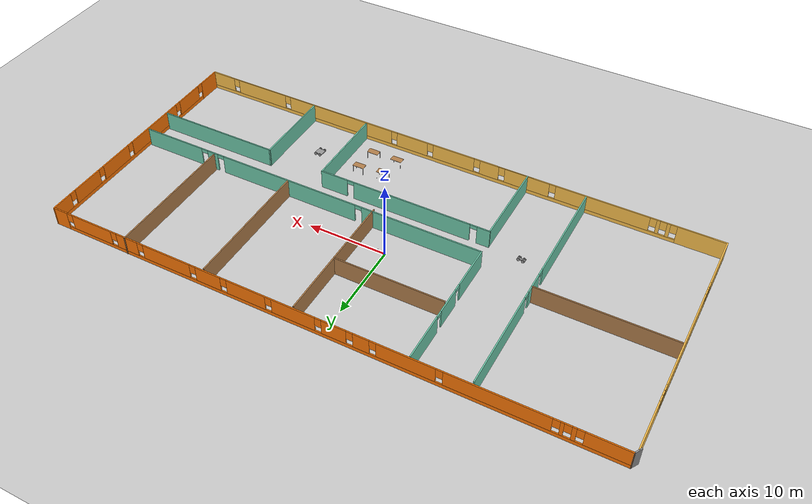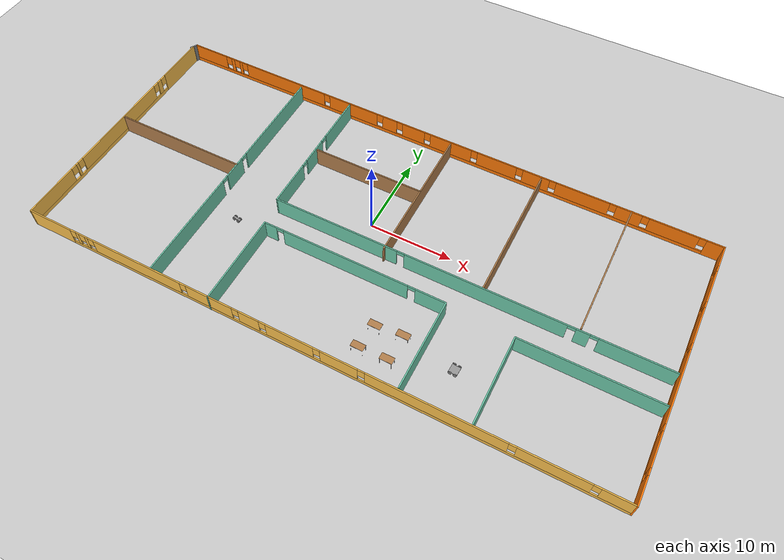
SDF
<sdf version="1.6">
 <world name="default">
  <plugin name="script" filename="libscript.so"/>
  <light name="sun" type="directional">
   <pose>0 0 10 0 -0 0</pose>
   <diffuse>0.8 0.8 0.8 1</diffuse>
   <specular>0.2 0.2 0.2 1</specular>
   <attenuation>
    <range>1000</range>
    <constant>0.9</constant>
    <linear>0.01</linear>
    <quadratic>0.001</quadratic>
   </attenuation>
   <direction>-0.5 0.1 -0.9</direction>
  </light>
  <model name="ground_plane">
   <static>1</static>
   <link name="link">
    <collision name="collision">
     <geometry><plane><normal>0 0 1</normal><size>100 100</size></plane></geometry>
     <surface>
      <contact><collide_bitmask>65535</collide_bitmask></contact>
      <friction><ode><mu>100</mu><mu2>50</mu2></ode></friction>
     </surface>
    </collision>
    <visual name="visual">
     <cast_shadows>0</cast_shadows>
     <geometry><plane><normal>0 0 1</normal><size>100 100</size></plane></geometry>
     <material>
      <script><uri>file://media/materials/scripts/gazebo.material</uri><name>Gazebo/Grey</name></script>
     </material>
    </visual>
   </link>
  </model>
  <gravity>0 0 -9.8</gravity>
  <magnetic_field>6e-06 2.3e-05 -4.2e-05</magnetic_field>
  <atmosphere type="adiabatic"/>
  <physics name="default_physics" default="0" type="ode">
   <max_step_size>0.001</max_step_size>
   <real_time_factor>1</real_time_factor>
   <real_time_update_rate>1000</real_time_update_rate>
  </physics>
  <scene><ambient>0.4 0.4 0.4 1</ambient><background>0.7 0.7 0.7 1</background><shadows>1</shadows></scene>
  <spherical_coordinates>
   <surface_model>EARTH_WGS84</surface_model>
   <latitude_deg>0</latitude_deg>
   <longitude_deg>0</longitude_deg>
   <elevation>0</elevation>
   <heading_deg>0</heading_deg>
  </spherical_coordinates>
  <model name="world">
   <pose>0.998 -1.93669 0 0 -0 0</pose>
   <link name="Wall_11">
    <pose>-18.4502 -0.168882 0 0 0 -1.5708</pose>
    <visual name="Wall_11_Visual_0">
     <pose>-9.3167 0 1.25 0 -0 0</pose>
     <geometry><box><size>12.8666 0.15 2.5</size></box></geometry>
     <material>
      <script><uri>file://media/materials/scripts/gazebo.material</uri><name>Gazebo/Grey</name></script>
      <ambient>0.435294 0.796078 0.67451 1</ambient>
     </material>
     <meta><layer>0</layer></meta>
    </visual>
    <collision name="Wall_11_Collision_0">
     <geometry><box><size>12.8666 0.15 2.5</size></box></geometry>
     <pose>-9.3167 0 1.25 0 -0 0</pose>
    </collision>
    <visual name="Wall_11_Visual_1">
     <pose>-0.463393 0 1.25 0 -0 0</pose>
     <geometry><box><size>3.04002 0.15 2.5</size></box></geometry>
     <material>
      <script><uri>file://media/materials/scripts/gazebo.material</uri><name>Gazebo/Grey</name></script>
      <ambient>0.435294 0.796078 0.67451 1</ambient>
     </material>
     <meta><layer>0</layer></meta>
    </visual>
    <collision name="Wall_11_Collision_1">
     <geometry><box><size>3.04002 0.15 2.5</size></box></geometry>
     <pose>-0.463393 0 1.25 0 -0 0</pose>
    </collision>
    <visual name="Wall_11_Visual_2">
     <pose>8.85331 0 1.25 0 -0 0</pose>
     <geometry><box><size>13.7934 0.15 2.5</size></box></geometry>
     <material>
      <script><uri>file://media/materials/scripts/gazebo.material</uri><name>Gazebo/Grey</name></script>
      <ambient>0.435294 0.796078 0.67451 1</ambient>
     </material>
     <meta><layer>0</layer></meta>
    </visual>
    <collision name="Wall_11_Collision_2">
     <geometry><box><size>13.7934 0.15 2.5</size></box></geometry>
     <pose>8.85331 0 1.25 0 -0 0</pose>
    </collision>
    <visual name="Wall_11_Visual_3">
     <pose>-2.4334 0 2.25 0 -0 0</pose>
     <geometry><box><size>0.9 0.15 0.5</size></box></geometry>
     <material>
      <script><uri>file://media/materials/scripts/gazebo.material</uri><name>Gazebo/Grey</name></script>
      <ambient>0.435294 0.796078 0.67451 1</ambient>
     </material>
     <meta><layer>0</layer></meta>
    </visual>
    <collision name="Wall_11_Collision_3">
     <geometry><box><size>0.9 0.15 0.5</size></box></geometry>
     <pose>-2.4334 0 2.25 0 -0 0</pose>
    </collision>
    <visual name="Wall_11_Visual_4">
     <pose>1.50662 0 2.25 0 -0 0</pose>
     <geometry><box><size>0.9 0.15 0.5</size></box></geometry>
     <material>
      <script><uri>file://media/materials/scripts/gazebo.material</uri><name>Gazebo/Grey</name></script>
      <ambient>0.435294 0.796078 0.67451 1</ambient>
     </material>
     <meta><layer>0</layer></meta>
    </visual>
    <collision name="Wall_11_Collision_4">
     <geometry><box><size>0.9 0.15 0.5</size></box></geometry>
     <pose>1.50662 0 2.25 0 -0 0</pose>
    </collision>
   </link>
   <link name="Wall_13">
    <pose>-11.4716 7.14221 0 0 0 -1.5708</pose>
    <visual name="Wall_13_Visual_0">
     <pose>-5.58135 0 1.25 0 -0 0</pose>
     <geometry><box><size>6.0873 0.15 2.5</size></box></geometry>
     <material>
      <script><uri>file://media/materials/scripts/gazebo.material</uri><name>Gazebo/Grey</name></script>
      <ambient>0.435294 0.796078 0.67451 1</ambient>
     </material>
     <meta><layer>0</layer></meta>
    </visual>
    <collision name="Wall_13_Collision_0">
     <geometry><box><size>6.0873 0.15 2.5</size></box></geometry>
     <pose>-5.58135 0 1.25 0 -0 0</pose>
    </collision>
    <visual name="Wall_13_Visual_1">
     <pose>0.128558 0 1.25 0 -0 0</pose>
     <geometry><box><size>3.53252 0.15 2.5</size></box></geometry>
     <material>
      <script><uri>file://media/materials/scripts/gazebo.material</uri><name>Gazebo/Grey</name></script>
      <ambient>0.435294 0.796078 0.67451 1</ambient>
     </material>
     <meta><layer>0</layer></meta>
    </visual>
    <collision name="Wall_13_Collision_1">
     <geometry><box><size>3.53252 0.15 2.5</size></box></geometry>
     <pose>0.128558 0 1.25 0 -0 0</pose>
    </collision>
    <visual name="Wall_13_Visual_2">
     <pose>5.70991 0 1.25 0 -0 0</pose>
     <geometry><box><size>5.83018 0.15 2.5</size></box></geometry>
     <material>
      <script><uri>file://media/materials/scripts/gazebo.material</uri><name>Gazebo/Grey</name></script>
      <ambient>0.435294 0.796078 0.67451 1</ambient>
     </material>
     <meta><layer>0</layer></meta>
    </visual>
    <collision name="Wall_13_Collision_2">
     <geometry><box><size>5.83018 0.15 2.5</size></box></geometry>
     <pose>5.70991 0 1.25 0 -0 0</pose>
    </collision>
    <visual name="Wall_13_Visual_3">
     <pose>-2.0877 0 2.25 0 -0 0</pose>
     <geometry><box><size>0.9 0.15 0.5</size></box></geometry>
     <material>
      <script><uri>file://media/materials/scripts/gazebo.material</uri><name>Gazebo/Grey</name></script>
      <ambient>0.435294 0.796078 0.67451 1</ambient>
     </material>
     <meta><layer>0</layer></meta>
    </visual>
    <collision name="Wall_13_Collision_3">
     <geometry><box><size>0.9 0.15 0.5</size></box></geometry>
     <pose>-2.0877 0 2.25 0 -0 0</pose>
    </collision>
    <visual name="Wall_13_Visual_4">
     <pose>2.34482 0 2.25 0 -0 0</pose>
     <geometry><box><size>0.9 0.15 0.5</size></box></geometry>
     <material>
      <script><uri>file://media/materials/scripts/gazebo.material</uri><name>Gazebo/Grey</name></script>
      <ambient>0.435294 0.796078 0.67451 1</ambient>
     </material>
     <meta><layer>0</layer></meta>
    </visual>
    <collision name="Wall_13_Collision_4">
     <geometry><box><size>0.9 0.15 0.5</size></box></geometry>
     <pose>2.34482 0 2.25 0 -0 0</pose>
    </collision>
   </link>
   <link name="Wall_14">
    <pose>11.8284 -1.40779 0 0 -0 0</pose>
    <visual name="Wall_14_Visual_0">
     <pose>-15.6414 0 1.25 0 -0 0</pose>
     <geometry><box><size>15.4671 0.15 2.5</size></box></geometry>
     <material>
      <script><uri>file://media/materials/scripts/gazebo.material</uri><name>Gazebo/Grey</name></script>
      <ambient>0.435294 0.796078 0.67451 1</ambient>
     </material>
     <meta><layer>0</layer></meta>
    </visual>
    <collision name="Wall_14_Collision_0">
     <geometry><box><size>15.4671 0.15 2.5</size></box></geometry>
     <pose>-15.6414 0 1.25 0 -0 0</pose>
    </collision>
    <visual name="Wall_14_Visual_1">
     <pose>2.37266 0 1.25 0 -0 0</pose>
     <geometry><box><size>18.761 0.15 2.5</size></box></geometry>
     <material>
      <script><uri>file://media/materials/scripts/gazebo.material</uri><name>Gazebo/Grey</name></script>
      <ambient>0.435294 0.796078 0.67451 1</ambient>
     </material>
     <meta><layer>0</layer></meta>
    </visual>
    <collision name="Wall_14_Collision_1">
     <geometry><box><size>18.761 0.15 2.5</size></box></geometry>
     <pose>2.37266 0 1.25 0 -0 0</pose>
    </collision>
    <visual name="Wall_14_Visual_2">
     <pose>13.406 0 1.25 0 -0 0</pose>
     <geometry><box><size>1.50558 0.15 2.5</size></box></geometry>
     <material>
      <script><uri>file://media/materials/scripts/gazebo.material</uri><name>Gazebo/Grey</name></script>
      <ambient>0.435294 0.796078 0.67451 1</ambient>
     </material>
     <meta><layer>0</layer></meta>
    </visual>
    <collision name="Wall_14_Collision_2">
     <geometry><box><size>1.50558 0.15 2.5</size></box></geometry>
     <pose>13.406 0 1.25 0 -0 0</pose>
    </collision>
    <visual name="Wall_14_Visual_3">
     <pose>19.2169 0 1.25 0 -0 0</pose>
     <geometry><box><size>8.31625 0.15 2.5</size></box></geometry>
     <material>
      <script><uri>file://media/materials/scripts/gazebo.material</uri><name>Gazebo/Grey</name></script>
      <ambient>0.435294 0.796078 0.67451 1</ambient>
     </material>
     <meta><layer>0</layer></meta>
    </visual>
    <collision name="Wall_14_Collision_3">
     <geometry><box><size>8.31625 0.15 2.5</size></box></geometry>
     <pose>19.2169 0 1.25 0 -0 0</pose>
    </collision>
    <visual name="Wall_14_Visual_4">
     <pose>-7.45785 0 2.25 0 -0 0</pose>
     <geometry><box><size>0.9 0.15 0.5</size></box></geometry>
     <material>
      <script><uri>file://media/materials/scripts/gazebo.material</uri><name>Gazebo/Grey</name></script>
      <ambient>0.435294 0.796078 0.67451 1</ambient>
     </material>
     <meta><layer>0</layer></meta>
    </visual>
    <collision name="Wall_14_Collision_4">
     <geometry><box><size>0.9 0.15 0.5</size></box></geometry>
     <pose>-7.45785 0 2.25 0 -0 0</pose>
    </collision>
    <visual name="Wall_14_Visual_5">
     <pose>12.2032 0 2.25 0 -0 0</pose>
     <geometry><box><size>0.9 0.15 0.5</size></box></geometry>
     <material>
      <script><uri>file://media/materials/scripts/gazebo.material</uri><name>Gazebo/Grey</name></script>
      <ambient>0.435294 0.796078 0.67451 1</ambient>
     </material>
     <meta><layer>0</layer></meta>
    </visual>
    <collision name="Wall_14_Collision_5">
     <geometry><box><size>0.9 0.15 0.5</size></box></geometry>
     <pose>12.2032 0 2.25 0 -0 0</pose>
    </collision>
    <visual name="Wall_14_Visual_6">
     <pose>14.6087 0 2.25 0 -0 0</pose>
     <geometry><box><size>0.9 0.15 0.5</size></box></geometry>
     <material>
      <script><uri>file://media/materials/scripts/gazebo.material</uri><name>Gazebo/Grey</name></script>
      <ambient>0.435294 0.796078 0.67451 1</ambient>
     </material>
     <meta><layer>0</layer></meta>
    </visual>
    <collision name="Wall_14_Collision_6">
     <geometry><box><size>0.9 0.15 0.5</size></box></geometry>
     <pose>14.6087 0 2.25 0 -0 0</pose>
    </collision>
   </link>
   <link name="Wall_16">
    <collision name="Wall_16_Collision">
     <geometry><box><size>17.5 0.15 2.5</size></box></geometry>
     <pose>0 0 1.25 0 -0 0</pose>
    </collision>
    <visual name="Wall_16_Visual">
     <pose>0 0 1.25 0 -0 0</pose>
     <geometry><box><size>17.5 0.15 2.5</size></box></geometry>
     <material>
      <script><uri>file://media/materials/scripts/gazebo.material</uri><name>Gazebo/Wood</name></script>
      <ambient>1 1 1 1</ambient>
     </material>
     <meta><layer>0</layer></meta>
    </visual>
    <pose>2.48559 6.92417 0 0 0 -1.5708</pose>
   </link>
   <link name="Wall_18">
    <collision name="Wall_18_Collision">
     <geometry><box><size>17 0.15 2.5</size></box></geometry>
     <pose>0 0 1.25 0 -0 0</pose>
    </collision>
    <visual name="Wall_18_Visual">
     <pose>0 0 1.25 0 -0 0</pose>
     <geometry><box><size>17 0.15 2.5</size></box></geometry>
     <material>
      <script><uri>file://media/materials/scripts/gazebo.material</uri><name>Gazebo/Wood</name></script>
      <ambient>1 1 1 1</ambient>
     </material>
     <meta><layer>0</layer></meta>
    </visual>
    <pose>14.1166 7.17417 0 0 0 -1.5708</pose>
   </link>
   <link name="Wall_20">
    <collision name="Wall_20_Collision">
     <geometry><box><size>17.25 0.15 2.5</size></box></geometry>
     <pose>0 0 1.25 0 -0 0</pose>
    </collision>
    <visual name="Wall_20_Visual">
     <pose>0 0 1.25 0 -0 0</pose>
     <geometry><box><size>17.25 0.15 2.5</size></box></geometry>
     <material>
      <script><uri>file://media/materials/scripts/gazebo.material</uri><name>Gazebo/Wood</name></script>
      <ambient>1 1 1 1</ambient>
     </material>
     <meta><layer>0</layer></meta>
    </visual>
    <pose>24.9101 7.42136 0 0 0 -1.5708</pose>
   </link>
   <link name="Wall_22">
    <collision name="Wall_22_Collision">
     <geometry><box><size>13.75 0.15 2.5</size></box></geometry>
     <pose>0 0 1.25 0 -0 0</pose>
    </collision>
    <visual name="Wall_22_Visual">
     <pose>0 0 1.25 0 -0 0</pose>
     <geometry><box><size>13.75 0.15 2.5</size></box></geometry>
     <material>
      <script><uri>file://media/materials/scripts/gazebo.material</uri><name>Gazebo/Wood</name></script>
      <ambient>1 1 1 1</ambient>
     </material>
     <meta><layer>0</layer></meta>
    </visual>
    <pose>-4.39243 7.31791 0 0 -0 0</pose>
   </link>
   <link name="Wall_24">
    <collision name="Wall_24_Collision">
     <geometry><box><size>11.25 0.15 2.5</size></box></geometry>
     <pose>0 0 1.25 0 -0 0</pose>
    </collision>
    <visual name="Wall_24_Visual">
     <pose>0 0 1.25 0 -0 0</pose>
     <geometry><box><size>11.25 0.15 2.5</size></box></geometry>
     <material>
      <script><uri>file://media/materials/scripts/gazebo.material</uri><name>Gazebo/Grey</name></script>
      <ambient>0.435294 0.796078 0.67451 1</ambient>
     </material>
     <meta><layer>0</layer></meta>
    </visual>
    <pose>-10.9133 -10.4214 0 0 0 -1.5708</pose>
   </link>
   <link name="Wall_26">
    <pose>0.261708 -4.87136 0 0 -0 0</pose>
    <visual name="Wall_26_Visual_0">
     <pose>-10.4274 0 1.25 0 -0 0</pose>
     <geometry><box><size>1.64525 0.15 2.5</size></box></geometry>
     <material>
      <script><uri>file://media/materials/scripts/gazebo.material</uri><name>Gazebo/Grey</name></script>
      <ambient>0.435294 0.796078 0.67451 1</ambient>
     </material>
     <meta><layer>0</layer></meta>
    </visual>
    <collision name="Wall_26_Collision_0">
     <geometry><box><size>1.64525 0.15 2.5</size></box></geometry>
     <pose>-10.4274 0 1.25 0 -0 0</pose>
    </collision>
    <visual name="Wall_26_Visual_1">
     <pose>-0.993281 0 1.25 0 -0 0</pose>
     <geometry><box><size>15.4229 0.15 2.5</size></box></geometry>
     <material>
      <script><uri>file://media/materials/scripts/gazebo.material</uri><name>Gazebo/Grey</name></script>
      <ambient>0.435294 0.796078 0.67451 1</ambient>
     </material>
     <meta><layer>0</layer></meta>
    </visual>
    <collision name="Wall_26_Collision_1">
     <geometry><box><size>15.4229 0.15 2.5</size></box></geometry>
     <pose>-0.993281 0 1.25 0 -0 0</pose>
    </collision>
    <visual name="Wall_26_Visual_2">
     <pose>9.4341 0 1.25 0 -0 0</pose>
     <geometry><box><size>3.63181 0.15 2.5</size></box></geometry>
     <material>
      <script><uri>file://media/materials/scripts/gazebo.material</uri><name>Gazebo/Grey</name></script>
      <ambient>0.435294 0.796078 0.67451 1</ambient>
     </material>
     <meta><layer>0</layer></meta>
    </visual>
    <collision name="Wall_26_Collision_2">
     <geometry><box><size>3.63181 0.15 2.5</size></box></geometry>
     <pose>9.4341 0 1.25 0 -0 0</pose>
    </collision>
    <visual name="Wall_26_Visual_3">
     <pose>-9.15475 0 2.25 0 -0 0</pose>
     <geometry><box><size>0.9 0.15 0.5</size></box></geometry>
     <material>
      <script><uri>file://media/materials/scripts/gazebo.material</uri><name>Gazebo/Grey</name></script>
      <ambient>0.435294 0.796078 0.67451 1</ambient>
     </material>
     <meta><layer>0</layer></meta>
    </visual>
    <collision name="Wall_26_Collision_3">
     <geometry><box><size>0.9 0.15 0.5</size></box></geometry>
     <pose>-9.15475 0 2.25 0 -0 0</pose>
    </collision>
    <visual name="Wall_26_Visual_4">
     <pose>7.16819 0 2.25 0 -0 0</pose>
     <geometry><box><size>0.9 0.15 0.5</size></box></geometry>
     <material>
      <script><uri>file://media/materials/scripts/gazebo.material</uri><name>Gazebo/Grey</name></script>
      <ambient>0.435294 0.796078 0.67451 1</ambient>
     </material>
     <meta><layer>0</layer></meta>
    </visual>
    <collision name="Wall_26_Collision_4">
     <geometry><box><size>0.9 0.15 0.5</size></box></geometry>
     <pose>7.16819 0 2.25 0 -0 0</pose>
    </collision>
   </link>
   <link name="Wall_27">
    <collision name="Wall_27_Collision">
     <geometry><box><size>11 0.15 2.5</size></box></geometry>
     <pose>0 0 1.25 0 -0 0</pose>
    </collision>
    <visual name="Wall_27_Visual">
     <pose>0 0 1.25 0 -0 0</pose>
     <geometry><box><size>11 0.15 2.5</size></box></geometry>
     <material>
      <script><uri>file://media/materials/scripts/gazebo.material</uri><name>Gazebo/Grey</name></script>
      <ambient>0.435294 0.796078 0.67451 1</ambient>
     </material>
     <meta><layer>0</layer></meta>
    </visual>
    <pose>11.4367 -10.2964 0 0 0 -1.5708</pose>
   </link>
   <link name="Wall_29">
    <collision name="Wall_29_Collision">
     <geometry><box><size>16 0.15 2.5</size></box></geometry>
     <pose>0 0 1.25 0 -0 0</pose>
    </collision>
    <visual name="Wall_29_Visual">
     <pose>0 0 1.25 0 -0 0</pose>
     <geometry><box><size>16 0.15 2.5</size></box></geometry>
     <material>
      <script><uri>file://media/materials/scripts/gazebo.material</uri><name>Gazebo/Grey</name></script>
      <ambient>0.435294 0.796078 0.67451 1</ambient>
     </material>
     <meta><layer>0</layer></meta>
    </visual>
    <pose>27.2523 -5.24355 0 0 -0 0</pose>
   </link>
   <link name="Wall_32">
    <collision name="Wall_32_Collision">
     <geometry><box><size>10.75 0.15 2.5</size></box></geometry>
     <pose>0 0 1.25 0 -0 0</pose>
    </collision>
    <visual name="Wall_32_Visual">
     <pose>0 0 1.25 0 -0 0</pose>
     <geometry><box><size>10.75 0.15 2.5</size></box></geometry>
     <material>
      <script><uri>file://media/materials/scripts/gazebo.material</uri><name>Gazebo/Grey</name></script>
      <ambient>0.435294 0.796078 0.67451 1</ambient>
     </material>
     <meta><layer>0</layer></meta>
    </visual>
    <pose>19.3273 -10.5435 0 0 0 -1.5708</pose>
   </link>
   <link name="Wall_34">
    <collision name="Wall_34_Collision">
     <geometry><box><size>16.75 0.15 2.5</size></box></geometry>
     <pose>0 0 1.25 0 -0 0</pose>
    </collision>
    <visual name="Wall_34_Visual">
     <pose>0 0 1.25 0 -0 0</pose>
     <geometry><box><size>16.75 0.15 2.5</size></box></geometry>
     <material>
      <script><uri>file://media/materials/scripts/gazebo.material</uri><name>Gazebo/Wood</name></script>
      <ambient>1 1 1 1</ambient>
     </material>
     <meta><layer>0</layer></meta>
    </visual>
    <pose>-26.8057 0.804561 0 0 -0 0</pose>
   </link>
   <link name="Wall_5">
    <pose>-35.1988 -0.26193 0 0 0 -1.5708</pose>
    <visual name="Wall_5_Visual_0">
     <pose>-12.5335 0 1.25 0 -0 0</pose>
     <geometry><box><size>6.43309 0.15 2.5</size></box></geometry>
     <material>
      <script><uri>file://media/materials/scripts/gazebo.material</uri><name>Gazebo/Grey</name></script>
      <ambient>1 0.764706 0.305882 1</ambient>
     </material>
     <meta><layer>0</layer></meta>
    </visual>
    <collision name="Wall_5_Collision_0">
     <geometry><box><size>6.43309 0.15 2.5</size></box></geometry>
     <pose>-12.5335 0 1.25 0 -0 0</pose>
    </collision>
    <visual name="Wall_5_Visual_1">
     <pose>3.21654 0 0.25 0 -0 0</pose>
     <geometry><box><size>25.0669 0.15 0.5</size></box></geometry>
     <material>
      <script><uri>file://media/materials/scripts/gazebo.material</uri><name>Gazebo/Grey</name></script>
      <ambient>1 0.764706 0.305882 1</ambient>
     </material>
     <meta><layer>0</layer></meta>
    </visual>
    <collision name="Wall_5_Collision_1">
     <geometry><box><size>25.0669 0.15 0.5</size></box></geometry>
     <pose>3.21654 0 0.25 0 -0 0</pose>
    </collision>
    <visual name="Wall_5_Visual_2">
     <pose>-8.17816 0 1.5 0 -0 0</pose>
     <geometry><box><size>0.677508 0.15 2</size></box></geometry>
     <material>
      <script><uri>file://media/materials/scripts/gazebo.material</uri><name>Gazebo/Grey</name></script>
      <ambient>1 0.764706 0.305882 1</ambient>
     </material>
     <meta><layer>0</layer></meta>
    </visual>
    <collision name="Wall_5_Collision_2">
     <geometry><box><size>0.677508 0.15 2</size></box></geometry>
     <pose>-8.17816 0 1.5 0 -0 0</pose>
    </collision>
    <visual name="Wall_5_Visual_3">
     <pose>-0.127812 0 1.5 0 -0 0</pose>
     <geometry><box><size>13.8232 0.15 2</size></box></geometry>
     <material>
      <script><uri>file://media/materials/scripts/gazebo.material</uri><name>Gazebo/Grey</name></script>
      <ambient>1 0.764706 0.305882 1</ambient>
     </material>
     <meta><layer>0</layer></meta>
    </visual>
    <collision name="Wall_5_Collision_3">
     <geometry><box><size>13.8232 0.15 2</size></box></geometry>
     <pose>-0.127812 0 1.5 0 -0 0</pose>
    </collision>
    <visual name="Wall_5_Visual_4">
     <pose>7.76499 0 1.5 0 -0 0</pose>
     <geometry><box><size>0.362429 0.15 2</size></box></geometry>
     <material>
      <script><uri>file://media/materials/scripts/gazebo.material</uri><name>Gazebo/Grey</name></script>
      <ambient>1 0.764706 0.305882 1</ambient>
     </material>
     <meta><layer>0</layer></meta>
    </visual>
    <collision name="Wall_5_Collision_4">
     <geometry><box><size>0.362429 0.15 2</size></box></geometry>
     <pose>7.76499 0 1.5 0 -0 0</pose>
    </collision>
    <visual name="Wall_5_Visual_5">
     <pose>12.2481 0 1.5 0 -0 0</pose>
     <geometry><box><size>7.00379 0.15 2</size></box></geometry>
     <material>
      <script><uri>file://media/materials/scripts/gazebo.material</uri><name>Gazebo/Grey</name></script>
      <ambient>1 0.764706 0.305882 1</ambient>
     </material>
     <meta><layer>0</layer></meta>
    </visual>
    <collision name="Wall_5_Collision_5">
     <geometry><box><size>7.00379 0.15 2</size></box></geometry>
     <pose>12.2481 0 1.5 0 -0 0</pose>
    </collision>
    <visual name="Wall_5_Visual_6">
     <pose>-8.91691 0 1.9 0 -0 0</pose>
     <geometry><box><size>0.8 0.15 1.2</size></box></geometry>
     <material>
      <script><uri>file://media/materials/scripts/gazebo.material</uri><name>Gazebo/Grey</name></script>
      <ambient>1 0.764706 0.305882 1</ambient>
     </material>
     <meta><layer>0</layer></meta>
    </visual>
    <collision name="Wall_5_Collision_6">
     <geometry><box><size>0.8 0.15 1.2</size></box></geometry>
     <pose>-8.91691 0 1.9 0 -0 0</pose>
    </collision>
    <visual name="Wall_5_Visual_7">
     <pose>-7.4394 0 1.9 0 -0 0</pose>
     <geometry><box><size>0.8 0.15 1.2</size></box></geometry>
     <material>
      <script><uri>file://media/materials/scripts/gazebo.material</uri><name>Gazebo/Grey</name></script>
      <ambient>1 0.764706 0.305882 1</ambient>
     </material>
     <meta><layer>0</layer></meta>
    </visual>
    <collision name="Wall_5_Collision_7">
     <geometry><box><size>0.8 0.15 1.2</size></box></geometry>
     <pose>-7.4394 0 1.9 0 -0 0</pose>
    </collision>
    <visual name="Wall_5_Visual_8">
     <pose>7.18378 0 1.9 0 -0 0</pose>
     <geometry><box><size>0.8 0.15 1.2</size></box></geometry>
     <material>
      <script><uri>file://media/materials/scripts/gazebo.material</uri><name>Gazebo/Grey</name></script>
      <ambient>1 0.764706 0.305882 1</ambient>
     </material>
     <meta><layer>0</layer></meta>
    </visual>
    <collision name="Wall_5_Collision_8">
     <geometry><box><size>0.8 0.15 1.2</size></box></geometry>
     <pose>7.18378 0 1.9 0 -0 0</pose>
    </collision>
    <visual name="Wall_5_Visual_9">
     <pose>8.34621 0 1.9 0 -0 0</pose>
     <geometry><box><size>0.8 0.15 1.2</size></box></geometry>
     <material>
      <script><uri>file://media/materials/scripts/gazebo.material</uri><name>Gazebo/Grey</name></script>
      <ambient>1 0.764706 0.305882 1</ambient>
     </material>
     <meta><layer>0</layer></meta>
    </visual>
    <collision name="Wall_5_Collision_9">
     <geometry><box><size>0.8 0.15 1.2</size></box></geometry>
     <pose>8.34621 0 1.9 0 -0 0</pose>
    </collision>
   </link>
   <link name="Wall_6">
    <pose>0.101225 -15.9369 0 0 -0 0</pose>
    <visual name="Wall_6_Visual_0">
     <pose>-32.4811 0 1.25 0 -0 0</pose>
     <geometry><box><size>5.78775 0.15 2.5</size></box></geometry>
     <material>
      <script><uri>file://media/materials/scripts/gazebo.material</uri><name>Gazebo/Grey</name></script>
      <ambient>1 0.764706 0.305882 1</ambient>
     </material>
     <meta><layer>0</layer></meta>
    </visual>
    <collision name="Wall_6_Collision_0">
     <geometry><box><size>5.78775 0.15 2.5</size></box></geometry>
     <pose>-32.4811 0 1.25 0 -0 0</pose>
    </collision>
    <visual name="Wall_6_Visual_1">
     <pose>2.89388 0 0.25 0 -0 0</pose>
     <geometry><box><size>64.9622 0.15 0.5</size></box></geometry>
     <material>
      <script><uri>file://media/materials/scripts/gazebo.material</uri><name>Gazebo/Grey</name></script>
      <ambient>1 0.764706 0.305882 1</ambient>
     </material>
     <meta><layer>0</layer></meta>
    </visual>
    <collision name="Wall_6_Collision_1">
     <geometry><box><size>64.9622 0.15 0.5</size></box></geometry>
     <pose>2.89388 0 0.25 0 -0 0</pose>
    </collision>
    <visual name="Wall_6_Visual_2">
     <pose>-28.5804 0 1.5 0 -0 0</pose>
     <geometry><box><size>0.413667 0.15 2</size></box></geometry>
     <material>
      <script><uri>file://media/materials/scripts/gazebo.material</uri><name>Gazebo/Grey</name></script>
      <ambient>1 0.764706 0.305882 1</ambient>
     </material>
     <meta><layer>0</layer></meta>
    </visual>
    <collision name="Wall_6_Collision_2">
     <geometry><box><size>0.413667 0.15 2</size></box></geometry>
     <pose>-28.5804 0 1.5 0 -0 0</pose>
    </collision>
    <visual name="Wall_6_Visual_3">
     <pose>-27.3667 0 1.5 0 -0 0</pose>
     <geometry><box><size>0.413667 0.15 2</size></box></geometry>
     <material>
      <script><uri>file://media/materials/scripts/gazebo.material</uri><name>Gazebo/Grey</name></script>
      <ambient>1 0.764706 0.305882 1</ambient>
     </material>
     <meta><layer>0</layer></meta>
    </visual>
    <collision name="Wall_6_Collision_3">
     <geometry><box><size>0.413667 0.15 2</size></box></geometry>
     <pose>-27.3667 0 1.5 0 -0 0</pose>
    </collision>
    <visual name="Wall_6_Visual_4">
     <pose>-20.5298 0 1.5 0 -0 0</pose>
     <geometry><box><size>11.6603 0.15 2</size></box></geometry>
     <material>
      <script><uri>file://media/materials/scripts/gazebo.material</uri><name>Gazebo/Grey</name></script>
      <ambient>1 0.764706 0.305882 1</ambient>
     </material>
     <meta><layer>0</layer></meta>
    </visual>
    <collision name="Wall_6_Collision_4">
     <geometry><box><size>11.6603 0.15 2</size></box></geometry>
     <pose>-20.5298 0 1.5 0 -0 0</pose>
    </collision>
    <visual name="Wall_6_Visual_5">
     <pose>-10.9822 0 1.5 0 -0 0</pose>
     <geometry><box><size>5.83472 0.15 2</size></box></geometry>
     <material>
      <script><uri>file://media/materials/scripts/gazebo.material</uri><name>Gazebo/Grey</name></script>
      <ambient>1 0.764706 0.305882 1</ambient>
     </material>
     <meta><layer>0</layer></meta>
    </visual>
    <collision name="Wall_6_Collision_5">
     <geometry><box><size>5.83472 0.15 2</size></box></geometry>
     <pose>-10.9822 0 1.5 0 -0 0</pose>
    </collision>
    <visual name="Wall_6_Visual_6">
     <pose>-5.99726 0 1.5 0 -0 0</pose>
     <geometry><box><size>2.53524 0.15 2</size></box></geometry>
     <material>
      <script><uri>file://media/materials/scripts/gazebo.material</uri><name>Gazebo/Grey</name></script>
      <ambient>1 0.764706 0.305882 1</ambient>
     </material>
     <meta><layer>0</layer></meta>
    </visual>
    <collision name="Wall_6_Collision_6">
     <geometry><box><size>2.53524 0.15 2</size></box></geometry>
     <pose>-5.99726 0 1.5 0 -0 0</pose>
    </collision>
    <visual name="Wall_6_Visual_7">
     <pose>-1.09549 0 1.5 0 -0 0</pose>
     <geometry><box><size>5.66831 0.15 2</size></box></geometry>
     <material>
      <script><uri>file://media/materials/scripts/gazebo.material</uri><name>Gazebo/Grey</name></script>
      <ambient>1 0.764706 0.305882 1</ambient>
     </material>
     <meta><layer>0</layer></meta>
    </visual>
    <collision name="Wall_6_Collision_7">
     <geometry><box><size>5.66831 0.15 2</size></box></geometry>
     <pose>-1.09549 0 1.5 0 -0 0</pose>
    </collision>
    <visual name="Wall_6_Visual_8">
     <pose>4.69748 0 1.5 0 -0 0</pose>
     <geometry><box><size>4.31763 0.15 2</size></box></geometry>
     <material>
      <script><uri>file://media/materials/scripts/gazebo.material</uri><name>Gazebo/Grey</name></script>
      <ambient>1 0.764706 0.305882 1</ambient>
     </material>
     <meta><layer>0</layer></meta>
    </visual>
    <collision name="Wall_6_Collision_8">
     <geometry><box><size>4.31763 0.15 2</size></box></geometry>
     <pose>4.69748 0 1.5 0 -0 0</pose>
    </collision>
    <visual name="Wall_6_Visual_9">
     <pose>15.3167 0 1.5 0 -0 0</pose>
     <geometry><box><size>15.3208 0.15 2</size></box></geometry>
     <material>
      <script><uri>file://media/materials/scripts/gazebo.material</uri><name>Gazebo/Grey</name></script>
      <ambient>1 0.764706 0.305882 1</ambient>
     </material>
     <meta><layer>0</layer></meta>
    </visual>
    <collision name="Wall_6_Collision_9">
     <geometry><box><size>15.3208 0.15 2</size></box></geometry>
     <pose>15.3167 0 1.5 0 -0 0</pose>
    </collision>
    <visual name="Wall_6_Visual_10">
     <pose>27.4964 0 1.5 0 -0 0</pose>
     <geometry><box><size>7.43877 0.15 2</size></box></geometry>
     <material>
      <script><uri>file://media/materials/scripts/gazebo.material</uri><name>Gazebo/Grey</name></script>
      <ambient>1 0.764706 0.305882 1</ambient>
     </material>
     <meta><layer>0</layer></meta>
    </visual>
    <collision name="Wall_6_Collision_10">
     <geometry><box><size>7.43877 0.15 2</size></box></geometry>
     <pose>27.4964 0 1.5 0 -0 0</pose>
    </collision>
    <visual name="Wall_6_Visual_11">
     <pose>33.6954 0 1.5 0 -0 0</pose>
     <geometry><box><size>3.35917 0.15 2</size></box></geometry>
     <material>
      <script><uri>file://media/materials/scripts/gazebo.material</uri><name>Gazebo/Grey</name></script>
      <ambient>1 0.764706 0.305882 1</ambient>
     </material>
     <meta><layer>0</layer></meta>
    </visual>
    <collision name="Wall_6_Collision_11">
     <geometry><box><size>3.35917 0.15 2</size></box></geometry>
     <pose>33.6954 0 1.5 0 -0 0</pose>
    </collision>
    <visual name="Wall_6_Visual_12">
     <pose>-29.1872 0 1.9 0 -0 0</pose>
     <geometry><box><size>0.8 0.15 1.2</size></box></geometry>
     <material>
      <script><uri>file://media/materials/scripts/gazebo.material</uri><name>Gazebo/Grey</name></script>
      <ambient>1 0.764706 0.305882 1</ambient>
     </material>
     <meta><layer>0</layer></meta>
    </visual>
    <collision name="Wall_6_Collision_12">
     <geometry><box><size>0.8 0.15 1.2</size></box></geometry>
     <pose>-29.1872 0 1.9 0 -0 0</pose>
    </collision>
    <visual name="Wall_6_Visual_13">
     <pose>-27.9736 0 1.9 0 -0 0</pose>
     <geometry><box><size>0.8 0.15 1.2</size></box></geometry>
     <material>
      <script><uri>file://media/materials/scripts/gazebo.material</uri><name>Gazebo/Grey</name></script>
      <ambient>1 0.764706 0.305882 1</ambient>
     </material>
     <meta><layer>0</layer></meta>
    </visual>
    <collision name="Wall_6_Collision_13">
     <geometry><box><size>0.8 0.15 1.2</size></box></geometry>
     <pose>-27.9736 0 1.9 0 -0 0</pose>
    </collision>
    <visual name="Wall_6_Visual_14">
     <pose>-26.7599 0 1.9 0 -0 0</pose>
     <geometry><box><size>0.8 0.15 1.2</size></box></geometry>
     <material>
      <script><uri>file://media/materials/scripts/gazebo.material</uri><name>Gazebo/Grey</name></script>
      <ambient>1 0.764706 0.305882 1</ambient>
     </material>
     <meta><layer>0</layer></meta>
    </visual>
    <collision name="Wall_6_Collision_14">
     <geometry><box><size>0.8 0.15 1.2</size></box></geometry>
     <pose>-26.7599 0 1.9 0 -0 0</pose>
    </collision>
    <visual name="Wall_6_Visual_15">
     <pose>-14.2996 0 1.9 0 -0 0</pose>
     <geometry><box><size>0.8 0.15 1.2</size></box></geometry>
     <material>
      <script><uri>file://media/materials/scripts/gazebo.material</uri><name>Gazebo/Grey</name></script>
      <ambient>1 0.764706 0.305882 1</ambient>
     </material>
     <meta><layer>0</layer></meta>
    </visual>
    <collision name="Wall_6_Collision_15">
     <geometry><box><size>0.8 0.15 1.2</size></box></geometry>
     <pose>-14.2996 0 1.9 0 -0 0</pose>
    </collision>
    <visual name="Wall_6_Visual_16">
     <pose>-7.66488 0 1.9 0 -0 0</pose>
     <geometry><box><size>0.8 0.15 1.2</size></box></geometry>
     <material>
      <script><uri>file://media/materials/scripts/gazebo.material</uri><name>Gazebo/Grey</name></script>
      <ambient>1 0.764706 0.305882 1</ambient>
     </material>
     <meta><layer>0</layer></meta>
    </visual>
    <collision name="Wall_6_Collision_16">
     <geometry><box><size>0.8 0.15 1.2</size></box></geometry>
     <pose>-7.66488 0 1.9 0 -0 0</pose>
    </collision>
    <visual name="Wall_6_Visual_17">
     <pose>-4.32964 0 1.9 0 -0 0</pose>
     <geometry><box><size>0.8 0.15 1.2</size></box></geometry>
     <material>
      <script><uri>file://media/materials/scripts/gazebo.material</uri><name>Gazebo/Grey</name></script>
      <ambient>1 0.764706 0.305882 1</ambient>
     </material>
     <meta><layer>0</layer></meta>
    </visual>
    <collision name="Wall_6_Collision_17">
     <geometry><box><size>0.8 0.15 1.2</size></box></geometry>
     <pose>-4.32964 0 1.9 0 -0 0</pose>
    </collision>
    <visual name="Wall_6_Visual_18">
     <pose>2.13867 0 1.9 0 -0 0</pose>
     <geometry><box><size>0.8 0.15 1.2</size></box></geometry>
     <material>
      <script><uri>file://media/materials/scripts/gazebo.material</uri><name>Gazebo/Grey</name></script>
      <ambient>1 0.764706 0.305882 1</ambient>
     </material>
     <meta><layer>0</layer></meta>
    </visual>
    <collision name="Wall_6_Collision_18">
     <geometry><box><size>0.8 0.15 1.2</size></box></geometry>
     <pose>2.13867 0 1.9 0 -0 0</pose>
    </collision>
    <visual name="Wall_6_Visual_19">
     <pose>7.2563 0 1.9 0 -0 0</pose>
     <geometry><box><size>0.8 0.15 1.2</size></box></geometry>
     <material>
      <script><uri>file://media/materials/scripts/gazebo.material</uri><name>Gazebo/Grey</name></script>
      <ambient>1 0.764706 0.305882 1</ambient>
     </material>
     <meta><layer>0</layer></meta>
    </visual>
    <collision name="Wall_6_Collision_19">
     <geometry><box><size>0.8 0.15 1.2</size></box></geometry>
     <pose>7.2563 0 1.9 0 -0 0</pose>
    </collision>
    <visual name="Wall_6_Visual_20">
     <pose>23.3771 0 1.9 0 -0 0</pose>
     <geometry><box><size>0.8 0.15 1.2</size></box></geometry>
     <material>
      <script><uri>file://media/materials/scripts/gazebo.material</uri><name>Gazebo/Grey</name></script>
      <ambient>1 0.764706 0.305882 1</ambient>
     </material>
     <meta><layer>0</layer></meta>
    </visual>
    <collision name="Wall_6_Collision_20">
     <geometry><box><size>0.8 0.15 1.2</size></box></geometry>
     <pose>23.3771 0 1.9 0 -0 0</pose>
    </collision>
    <visual name="Wall_6_Visual_21">
     <pose>31.6158 0 1.9 0 -0 0</pose>
     <geometry><box><size>0.8 0.15 1.2</size></box></geometry>
     <material>
      <script><uri>file://media/materials/scripts/gazebo.material</uri><name>Gazebo/Grey</name></script>
      <ambient>1 0.764706 0.305882 1</ambient>
     </material>
     <meta><layer>0</layer></meta>
    </visual>
    <collision name="Wall_6_Collision_21">
     <geometry><box><size>0.8 0.15 1.2</size></box></geometry>
     <pose>31.6158 0 1.9 0 -0 0</pose>
    </collision>
   </link>
   <link name="Wall_7">
    <pose>35.4012 -0.01193 0 0 -0 1.5708</pose>
    <visual name="Wall_7_Visual_0">
     <pose>-14.3843 0 1.25 0 -0 0</pose>
     <geometry><box><size>3.23139 0.15 2.5</size></box></geometry>
     <material>
      <script><uri>file://media/materials/scripts/gazebo.material</uri><name>Gazebo/Grey</name></script>
      <ambient>0.996078 0.47451 0.0196078 1</ambient>
     </material>
     <meta><layer>0</layer></meta>
    </visual>
    <collision name="Wall_7_Collision_0">
     <geometry><box><size>3.23139 0.15 2.5</size></box></geometry>
     <pose>-14.3843 0 1.25 0 -0 0</pose>
    </collision>
    <visual name="Wall_7_Visual_1">
     <pose>1.6157 0 0.25 0 -0 0</pose>
     <geometry><box><size>28.7686 0.15 0.5</size></box></geometry>
     <material>
      <script><uri>file://media/materials/scripts/gazebo.material</uri><name>Gazebo/Grey</name></script>
      <ambient>0.996078 0.47451 0.0196078 1</ambient>
     </material>
     <meta><layer>0</layer></meta>
    </visual>
    <collision name="Wall_7_Collision_1">
     <geometry><box><size>28.7686 0.15 0.5</size></box></geometry>
     <pose>1.6157 0 0.25 0 -0 0</pose>
    </collision>
    <visual name="Wall_7_Visual_2">
     <pose>-9.958 0 1.5 0 -0 0</pose>
     <geometry><box><size>4.02121 0.15 2</size></box></geometry>
     <material>
      <script><uri>file://media/materials/scripts/gazebo.material</uri><name>Gazebo/Grey</name></script>
      <ambient>0.996078 0.47451 0.0196078 1</ambient>
     </material>
     <meta><layer>0</layer></meta>
    </visual>
    <collision name="Wall_7_Collision_2">
     <geometry><box><size>4.02121 0.15 2</size></box></geometry>
     <pose>-9.958 0 1.5 0 -0 0</pose>
    </collision>
    <visual name="Wall_7_Visual_3">
     <pose>-2.67355 0 1.5 0 -0 0</pose>
     <geometry><box><size>8.9477 0.15 2</size></box></geometry>
     <material>
      <script><uri>file://media/materials/scripts/gazebo.material</uri><name>Gazebo/Grey</name></script>
      <ambient>0.996078 0.47451 0.0196078 1</ambient>
     </material>
     <meta><layer>0</layer></meta>
    </visual>
    <collision name="Wall_7_Collision_3">
     <geometry><box><size>8.9477 0.15 2</size></box></geometry>
     <pose>-2.67355 0 1.5 0 -0 0</pose>
    </collision>
    <visual name="Wall_7_Visual_4">
     <pose>4.95128 0 1.5 0 -0 0</pose>
     <geometry><box><size>4.70196 0.15 2</size></box></geometry>
     <material>
      <script><uri>file://media/materials/scripts/gazebo.material</uri><name>Gazebo/Grey</name></script>
      <ambient>0.996078 0.47451 0.0196078 1</ambient>
     </material>
     <meta><layer>0</layer></meta>
    </visual>
    <collision name="Wall_7_Collision_4">
     <geometry><box><size>4.70196 0.15 2</size></box></geometry>
     <pose>4.95128 0 1.5 0 -0 0</pose>
    </collision>
    <visual name="Wall_7_Visual_5">
     <pose>10.251 0 1.5 0 -0 0</pose>
     <geometry><box><size>4.2974 0.15 2</size></box></geometry>
     <material>
      <script><uri>file://media/materials/scripts/gazebo.material</uri><name>Gazebo/Grey</name></script>
      <ambient>0.996078 0.47451 0.0196078 1</ambient>
     </material>
     <meta><layer>0</layer></meta>
    </visual>
    <collision name="Wall_7_Collision_5">
     <geometry><box><size>4.2974 0.15 2</size></box></geometry>
     <pose>10.251 0 1.5 0 -0 0</pose>
    </collision>
    <visual name="Wall_7_Visual_6">
     <pose>14.5998 0 1.5 0 -0 0</pose>
     <geometry><box><size>2.80034 0.15 2</size></box></geometry>
     <material>
      <script><uri>file://media/materials/scripts/gazebo.material</uri><name>Gazebo/Grey</name></script>
      <ambient>0.996078 0.47451 0.0196078 1</ambient>
     </material>
     <meta><layer>0</layer></meta>
    </visual>
    <collision name="Wall_7_Collision_6">
     <geometry><box><size>2.80034 0.15 2</size></box></geometry>
     <pose>14.5998 0 1.5 0 -0 0</pose>
    </collision>
    <visual name="Wall_7_Visual_7">
     <pose>-12.3686 0 1.9 0 -0 0</pose>
     <geometry><box><size>0.8 0.15 1.2</size></box></geometry>
     <material>
      <script><uri>file://media/materials/scripts/gazebo.material</uri><name>Gazebo/Grey</name></script>
      <ambient>0.996078 0.47451 0.0196078 1</ambient>
     </material>
     <meta><layer>0</layer></meta>
    </visual>
    <collision name="Wall_7_Collision_7">
     <geometry><box><size>0.8 0.15 1.2</size></box></geometry>
     <pose>-12.3686 0 1.9 0 -0 0</pose>
    </collision>
    <visual name="Wall_7_Visual_8">
     <pose>-7.5474 0 1.9 0 -0 0</pose>
     <geometry><box><size>0.8 0.15 1.2</size></box></geometry>
     <material>
      <script><uri>file://media/materials/scripts/gazebo.material</uri><name>Gazebo/Grey</name></script>
      <ambient>0.996078 0.47451 0.0196078 1</ambient>
     </material>
     <meta><layer>0</layer></meta>
    </visual>
    <collision name="Wall_7_Collision_8">
     <geometry><box><size>0.8 0.15 1.2</size></box></geometry>
     <pose>-7.5474 0 1.9 0 -0 0</pose>
    </collision>
    <visual name="Wall_7_Visual_9">
     <pose>2.2003 0 1.9 0 -0 0</pose>
     <geometry><box><size>0.8 0.15 1.2</size></box></geometry>
     <material>
      <script><uri>file://media/materials/scripts/gazebo.material</uri><name>Gazebo/Grey</name></script>
      <ambient>0.996078 0.47451 0.0196078 1</ambient>
     </material>
     <meta><layer>0</layer></meta>
    </visual>
    <collision name="Wall_7_Collision_9">
     <geometry><box><size>0.8 0.15 1.2</size></box></geometry>
     <pose>2.2003 0 1.9 0 -0 0</pose>
    </collision>
    <visual name="Wall_7_Visual_10">
     <pose>7.70226 0 1.9 0 -0 0</pose>
     <geometry><box><size>0.8 0.15 1.2</size></box></geometry>
     <material>
      <script><uri>file://media/materials/scripts/gazebo.material</uri><name>Gazebo/Grey</name></script>
      <ambient>0.996078 0.47451 0.0196078 1</ambient>
     </material>
     <meta><layer>0</layer></meta>
    </visual>
    <collision name="Wall_7_Collision_10">
     <geometry><box><size>0.8 0.15 1.2</size></box></geometry>
     <pose>7.70226 0 1.9 0 -0 0</pose>
    </collision>
    <visual name="Wall_7_Visual_11">
     <pose>12.7997 0 1.9 0 -0 0</pose>
     <geometry><box><size>0.8 0.15 1.2</size></box></geometry>
     <material>
      <script><uri>file://media/materials/scripts/gazebo.material</uri><name>Gazebo/Grey</name></script>
      <ambient>0.996078 0.47451 0.0196078 1</ambient>
     </material>
     <meta><layer>0</layer></meta>
    </visual>
    <collision name="Wall_7_Collision_11">
     <geometry><box><size>0.8 0.15 1.2</size></box></geometry>
     <pose>12.7997 0 1.9 0 -0 0</pose>
    </collision>
   </link>
   <link name="Wall_8">
    <pose>0.226225 15.9131 0 0 -0 3.14159</pose>
    <visual name="Wall_8_Visual_0">
     <pose>-34.2388 0 1.25 0 -0 0</pose>
     <geometry><box><size>2.02248 0.15 2.5</size></box></geometry>
     <material>
      <script><uri>file://media/materials/scripts/gazebo.material</uri><name>Gazebo/Grey</name></script>
      <ambient>0.996078 0.47451 0.0196078 1</ambient>
     </material>
     <meta><layer>0</layer></meta>
    </visual>
    <collision name="Wall_8_Collision_0">
     <geometry><box><size>2.02248 0.15 2.5</size></box></geometry>
     <pose>-34.2388 0 1.25 0 -0 0</pose>
    </collision>
    <visual name="Wall_8_Visual_1">
     <pose>1.01124 0 0.25 0 -0 0</pose>
     <geometry><box><size>68.4775 0.15 0.5</size></box></geometry>
     <material>
      <script><uri>file://media/materials/scripts/gazebo.material</uri><name>Gazebo/Grey</name></script>
      <ambient>0.996078 0.47451 0.0196078 1</ambient>
     </material>
     <meta><layer>0</layer></meta>
    </visual>
    <collision name="Wall_8_Collision_1">
     <geometry><box><size>68.4775 0.15 0.5</size></box></geometry>
     <pose>1.01124 0 0.25 0 -0 0</pose>
    </collision>
    <visual name="Wall_8_Visual_2">
     <pose>-29.5911 0 1.5 0 -0 0</pose>
     <geometry><box><size>5.67289 0.15 2</size></box></geometry>
     <material>
      <script><uri>file://media/materials/scripts/gazebo.material</uri><name>Gazebo/Grey</name></script>
      <ambient>0.996078 0.47451 0.0196078 1</ambient>
     </material>
     <meta><layer>0</layer></meta>
    </visual>
    <collision name="Wall_8_Collision_2">
     <geometry><box><size>5.67289 0.15 2</size></box></geometry>
     <pose>-29.5911 0 1.5 0 -0 0</pose>
    </collision>
    <visual name="Wall_8_Visual_3">
     <pose>-24.4532 0 1.5 0 -0 0</pose>
     <geometry><box><size>3.00282 0.15 2</size></box></geometry>
     <material>
      <script><uri>file://media/materials/scripts/gazebo.material</uri><name>Gazebo/Grey</name></script>
      <ambient>0.996078 0.47451 0.0196078 1</ambient>
     </material>
     <meta><layer>0</layer></meta>
    </visual>
    <collision name="Wall_8_Collision_3">
     <geometry><box><size>3.00282 0.15 2</size></box></geometry>
     <pose>-24.4532 0 1.5 0 -0 0</pose>
    </collision>
    <visual name="Wall_8_Visual_4">
     <pose>-18.9108 0 1.5 0 -0 0</pose>
     <geometry><box><size>6.482 0.15 2</size></box></geometry>
     <material>
      <script><uri>file://media/materials/scripts/gazebo.material</uri><name>Gazebo/Grey</name></script>
      <ambient>0.996078 0.47451 0.0196078 1</ambient>
     </material>
     <meta><layer>0</layer></meta>
    </visual>
    <collision name="Wall_8_Collision_4">
     <geometry><box><size>6.482 0.15 2</size></box></geometry>
     <pose>-18.9108 0 1.5 0 -0 0</pose>
    </collision>
    <visual name="Wall_8_Visual_5">
     <pose>-13.2066 0 1.5 0 -0 0</pose>
     <geometry><box><size>3.32647 0.15 2</size></box></geometry>
     <material>
      <script><uri>file://media/materials/scripts/gazebo.material</uri><name>Gazebo/Grey</name></script>
      <ambient>0.996078 0.47451 0.0196078 1</ambient>
     </material>
     <meta><layer>0</layer></meta>
    </visual>
    <collision name="Wall_8_Collision_5">
     <geometry><box><size>3.32647 0.15 2</size></box></geometry>
     <pose>-13.2066 0 1.5 0 -0 0</pose>
    </collision>
    <visual name="Wall_8_Visual_6">
     <pose>-8.23053 0 1.5 0 -0 0</pose>
     <geometry><box><size>5.0256 0.15 2</size></box></geometry>
     <material>
      <script><uri>file://media/materials/scripts/gazebo.material</uri><name>Gazebo/Grey</name></script>
      <ambient>0.996078 0.47451 0.0196078 1</ambient>
     </material>
     <meta><layer>0</layer></meta>
    </visual>
    <collision name="Wall_8_Collision_6">
     <geometry><box><size>5.0256 0.15 2</size></box></geometry>
     <pose>-8.23053 0 1.5 0 -0 0</pose>
    </collision>
    <visual name="Wall_8_Visual_7">
     <pose>-2.20265 0 1.5 0 -0 0</pose>
     <geometry><box><size>5.43016 0.15 2</size></box></geometry>
     <material>
      <script><uri>file://media/materials/scripts/gazebo.material</uri><name>Gazebo/Grey</name></script>
      <ambient>0.996078 0.47451 0.0196078 1</ambient>
     </material>
     <meta><layer>0</layer></meta>
    </visual>
    <collision name="Wall_8_Collision_7">
     <geometry><box><size>5.43016 0.15 2</size></box></geometry>
     <pose>-2.20265 0 1.5 0 -0 0</pose>
    </collision>
    <visual name="Wall_8_Visual_8">
     <pose>2.81385 0 1.5 0 -0 0</pose>
     <geometry><box><size>3.00282 0.15 2</size></box></geometry>
     <material>
      <script><uri>file://media/materials/scripts/gazebo.material</uri><name>Gazebo/Grey</name></script>
      <ambient>0.996078 0.47451 0.0196078 1</ambient>
     </material>
     <meta><layer>0</layer></meta>
    </visual>
    <collision name="Wall_8_Collision_8">
     <geometry><box><size>3.00282 0.15 2</size></box></geometry>
     <pose>2.81385 0 1.5 0 -0 0</pose>
    </collision>
    <visual name="Wall_8_Visual_9">
     <pose>6.09075 0 1.5 0 -0 0</pose>
     <geometry><box><size>1.95098 0.15 2</size></box></geometry>
     <material>
      <script><uri>file://media/materials/scripts/gazebo.material</uri><name>Gazebo/Grey</name></script>
      <ambient>0.996078 0.47451 0.0196078 1</ambient>
     </material>
     <meta><layer>0</layer></meta>
    </visual>
    <collision name="Wall_8_Collision_9">
     <geometry><box><size>1.95098 0.15 2</size></box></geometry>
     <pose>6.09075 0 1.5 0 -0 0</pose>
    </collision>
    <visual name="Wall_8_Visual_10">
     <pose>11.2691 0 1.5 0 -0 0</pose>
     <geometry><box><size>6.80565 0.15 2</size></box></geometry>
     <material>
      <script><uri>file://media/materials/scripts/gazebo.material</uri><name>Gazebo/Grey</name></script>
      <ambient>0.996078 0.47451 0.0196078 1</ambient>
     </material>
     <meta><layer>0</layer></meta>
    </visual>
    <collision name="Wall_8_Collision_10">
     <geometry><box><size>6.80565 0.15 2</size></box></geometry>
     <pose>11.2691 0 1.5 0 -0 0</pose>
    </collision>
    <visual name="Wall_8_Visual_11">
     <pose>21.2909 0 1.5 0 -0 0</pose>
     <geometry><box><size>11.6381 0.15 2</size></box></geometry>
     <material>
      <script><uri>file://media/materials/scripts/gazebo.material</uri><name>Gazebo/Grey</name></script>
      <ambient>0.996078 0.47451 0.0196078 1</ambient>
     </material>
     <meta><layer>0</layer></meta>
    </visual>
    <collision name="Wall_8_Collision_11">
     <geometry><box><size>11.6381 0.15 2</size></box></geometry>
     <pose>21.2909 0 1.5 0 -0 0</pose>
    </collision>
    <visual name="Wall_8_Visual_12">
     <pose>28.108 0 1.5 0 -0 0</pose>
     <geometry><box><size>0.396077 0.15 2</size></box></geometry>
     <material>
      <script><uri>file://media/materials/scripts/gazebo.material</uri><name>Gazebo/Grey</name></script>
      <ambient>0.996078 0.47451 0.0196078 1</ambient>
     </material>
     <meta><layer>0</layer></meta>
    </visual>
    <collision name="Wall_8_Collision_12">
     <geometry><box><size>0.396077 0.15 2</size></box></geometry>
     <pose>28.108 0 1.5 0 -0 0</pose>
    </collision>
    <visual name="Wall_8_Visual_13">
     <pose>29.3393 0 1.5 0 -0 0</pose>
     <geometry><box><size>0.466436 0.15 2</size></box></geometry>
     <material>
      <script><uri>file://media/materials/scripts/gazebo.material</uri><name>Gazebo/Grey</name></script>
      <ambient>0.996078 0.47451 0.0196078 1</ambient>
     </material>
     <meta><layer>0</layer></meta>
    </visual>
    <collision name="Wall_8_Collision_13">
     <geometry><box><size>0.466436 0.15 2</size></box></geometry>
     <pose>29.3393 0 1.5 0 -0 0</pose>
    </collision>
    <visual name="Wall_8_Visual_14">
     <pose>32.8113 0 1.5 0 -0 0</pose>
     <geometry><box><size>4.87747 0.15 2</size></box></geometry>
     <material>
      <script><uri>file://media/materials/scripts/gazebo.material</uri><name>Gazebo/Grey</name></script>
      <ambient>0.996078 0.47451 0.0196078 1</ambient>
     </material>
     <meta><layer>0</layer></meta>
    </visual>
    <collision name="Wall_8_Collision_14">
     <geometry><box><size>4.87747 0.15 2</size></box></geometry>
     <pose>32.8113 0 1.5 0 -0 0</pose>
    </collision>
    <visual name="Wall_8_Visual_15">
     <pose>-32.8275 0 1.9 0 -0 0</pose>
     <geometry><box><size>0.8 0.15 1.2</size></box></geometry>
     <material>
      <script><uri>file://media/materials/scripts/gazebo.material</uri><name>Gazebo/Grey</name></script>
      <ambient>0.996078 0.47451 0.0196078 1</ambient>
     </material>
     <meta><layer>0</layer></meta>
    </visual>
    <collision name="Wall_8_Collision_15">
     <geometry><box><size>0.8 0.15 1.2</size></box></geometry>
     <pose>-32.8275 0 1.9 0 -0 0</pose>
    </collision>
    <visual name="Wall_8_Visual_16">
     <pose>-26.3546 0 1.9 0 -0 0</pose>
     <geometry><box><size>0.8 0.15 1.2</size></box></geometry>
     <material>
      <script><uri>file://media/materials/scripts/gazebo.material</uri><name>Gazebo/Grey</name></script>
      <ambient>0.996078 0.47451 0.0196078 1</ambient>
     </material>
     <meta><layer>0</layer></meta>
    </visual>
    <collision name="Wall_8_Collision_16">
     <geometry><box><size>0.8 0.15 1.2</size></box></geometry>
     <pose>-26.3546 0 1.9 0 -0 0</pose>
    </collision>
    <visual name="Wall_8_Visual_17">
     <pose>-22.5518 0 1.9 0 -0 0</pose>
     <geometry><box><size>0.8 0.15 1.2</size></box></geometry>
     <material>
      <script><uri>file://media/materials/scripts/gazebo.material</uri><name>Gazebo/Grey</name></script>
      <ambient>0.996078 0.47451 0.0196078 1</ambient>
     </material>
     <meta><layer>0</layer></meta>
    </visual>
    <collision name="Wall_8_Collision_17">
     <geometry><box><size>0.8 0.15 1.2</size></box></geometry>
     <pose>-22.5518 0 1.9 0 -0 0</pose>
    </collision>
    <visual name="Wall_8_Visual_18">
     <pose>-15.2698 0 1.9 0 -0 0</pose>
     <geometry><box><size>0.8 0.15 1.2</size></box></geometry>
     <material>
      <script><uri>file://media/materials/scripts/gazebo.material</uri><name>Gazebo/Grey</name></script>
      <ambient>0.996078 0.47451 0.0196078 1</ambient>
     </material>
     <meta><layer>0</layer></meta>
    </visual>
    <collision name="Wall_8_Collision_18">
     <geometry><box><size>0.8 0.15 1.2</size></box></geometry>
     <pose>-15.2698 0 1.9 0 -0 0</pose>
    </collision>
    <visual name="Wall_8_Visual_19">
     <pose>-11.1433 0 1.9 0 -0 0</pose>
     <geometry><box><size>0.8 0.15 1.2</size></box></geometry>
     <material>
      <script><uri>file://media/materials/scripts/gazebo.material</uri><name>Gazebo/Grey</name></script>
      <ambient>0.996078 0.47451 0.0196078 1</ambient>
     </material>
     <meta><layer>0</layer></meta>
    </visual>
    <collision name="Wall_8_Collision_19">
     <geometry><box><size>0.8 0.15 1.2</size></box></geometry>
     <pose>-11.1433 0 1.9 0 -0 0</pose>
    </collision>
    <visual name="Wall_8_Visual_20">
     <pose>-5.31773 0 1.9 0 -0 0</pose>
     <geometry><box><size>0.8 0.15 1.2</size></box></geometry>
     <material>
      <script><uri>file://media/materials/scripts/gazebo.material</uri><name>Gazebo/Grey</name></script>
      <ambient>0.996078 0.47451 0.0196078 1</ambient>
     </material>
     <meta><layer>0</layer></meta>
    </visual>
    <collision name="Wall_8_Collision_20">
     <geometry><box><size>0.8 0.15 1.2</size></box></geometry>
     <pose>-5.31773 0 1.9 0 -0 0</pose>
    </collision>
    <visual name="Wall_8_Visual_21">
     <pose>0.912433 0 1.9 0 -0 0</pose>
     <geometry><box><size>0.8 0.15 1.2</size></box></geometry>
     <material>
      <script><uri>file://media/materials/scripts/gazebo.material</uri><name>Gazebo/Grey</name></script>
      <ambient>0.996078 0.47451 0.0196078 1</ambient>
     </material>
     <meta><layer>0</layer></meta>
    </visual>
    <collision name="Wall_8_Collision_21">
     <geometry><box><size>0.8 0.15 1.2</size></box></geometry>
     <pose>0.912433 0 1.9 0 -0 0</pose>
    </collision>
    <visual name="Wall_8_Visual_22">
     <pose>4.71526 0 1.9 0 -0 0</pose>
     <geometry><box><size>0.8 0.15 1.2</size></box></geometry>
     <material>
      <script><uri>file://media/materials/scripts/gazebo.material</uri><name>Gazebo/Grey</name></script>
      <ambient>0.996078 0.47451 0.0196078 1</ambient>
     </material>
     <meta><layer>0</layer></meta>
    </visual>
    <collision name="Wall_8_Collision_22">
     <geometry><box><size>0.8 0.15 1.2</size></box></geometry>
     <pose>4.71526 0 1.9 0 -0 0</pose>
    </collision>
    <visual name="Wall_8_Visual_23">
     <pose>7.46624 0 1.9 0 -0 0</pose>
     <geometry><box><size>0.8 0.15 1.2</size></box></geometry>
     <material>
      <script><uri>file://media/materials/scripts/gazebo.material</uri><name>Gazebo/Grey</name></script>
      <ambient>0.996078 0.47451 0.0196078 1</ambient>
     </material>
     <meta><layer>0</layer></meta>
    </visual>
    <collision name="Wall_8_Collision_23">
     <geometry><box><size>0.8 0.15 1.2</size></box></geometry>
     <pose>7.46624 0 1.9 0 -0 0</pose>
    </collision>
    <visual name="Wall_8_Visual_24">
     <pose>15.0719 0 1.9 0 -0 0</pose>
     <geometry><box><size>0.8 0.15 1.2</size></box></geometry>
     <material>
      <script><uri>file://media/materials/scripts/gazebo.material</uri><name>Gazebo/Grey</name></script>
      <ambient>0.996078 0.47451 0.0196078 1</ambient>
     </material>
     <meta><layer>0</layer></meta>
    </visual>
    <collision name="Wall_8_Collision_24">
     <geometry><box><size>0.8 0.15 1.2</size></box></geometry>
     <pose>15.0719 0 1.9 0 -0 0</pose>
    </collision>
    <visual name="Wall_8_Visual_25">
     <pose>27.51 0 1.9 0 -0 0</pose>
     <geometry><box><size>0.8 0.15 1.2</size></box></geometry>
     <material>
      <script><uri>file://media/materials/scripts/gazebo.material</uri><name>Gazebo/Grey</name></script>
      <ambient>0.996078 0.47451 0.0196078 1</ambient>
     </material>
     <meta><layer>0</layer></meta>
    </visual>
    <collision name="Wall_8_Collision_25">
     <geometry><box><size>0.8 0.15 1.2</size></box></geometry>
     <pose>27.51 0 1.9 0 -0 0</pose>
    </collision>
    <visual name="Wall_8_Visual_26">
     <pose>28.7061 0 1.9 0 -0 0</pose>
     <geometry><box><size>0.8 0.15 1.2</size></box></geometry>
     <material>
      <script><uri>file://media/materials/scripts/gazebo.material</uri><name>Gazebo/Grey</name></script>
      <ambient>0.996078 0.47451 0.0196078 1</ambient>
     </material>
     <meta><layer>0</layer></meta>
    </visual>
    <collision name="Wall_8_Collision_26">
     <geometry><box><size>0.8 0.15 1.2</size></box></geometry>
     <pose>28.7061 0 1.9 0 -0 0</pose>
    </collision>
    <visual name="Wall_8_Visual_27">
     <pose>29.9725 0 1.9 0 -0 0</pose>
     <geometry><box><size>0.8 0.15 1.2</size></box></geometry>
     <material>
      <script><uri>file://media/materials/scripts/gazebo.material</uri><name>Gazebo/Grey</name></script>
      <ambient>0.996078 0.47451 0.0196078 1</ambient>
     </material>
     <meta><layer>0</layer></meta>
    </visual>
    <collision name="Wall_8_Collision_27">
     <geometry><box><size>0.8 0.15 1.2</size></box></geometry>
     <pose>29.9725 0 1.9 0 -0 0</pose>
    </collision>
   </link>
   <link name="Wall_9">
    <collision name="Wall_9_Collision">
     <geometry><box><size>1 0.15 2.5</size></box></geometry>
     <pose>0 0 1.25 0 -0 0</pose>
    </collision>
    <visual name="Wall_9_Visual">
     <pose>0 0 1.25 0 -0 0</pose>
     <geometry><box><size>1 0.15 2.5</size></box></geometry>
     <material>
      <script><uri>file://media/materials/scripts/gazebo.material</uri><name>Gazebo/Grey</name></script>
      <ambient>1 1 1 1</ambient>
     </material>
     <meta><layer>0</layer></meta>
    </visual>
    <pose>-35.1613 15.545 0 0 0 -2.0944</pose>
   </link>
   <static>1</static>
  </model>
  <model name="table">
   <static>1</static>
   <link name="link">
    <collision name="surface">
     <pose>0 0 1 0 -0 0</pose>
     <geometry><box><size>1.5 0.8 0.03</size></box></geometry>
     <surface><friction><ode><mu>0.6</mu><mu2>0.6</mu2></ode></friction></surface>
    </collision>
    <visual name="visual1">
     <pose>0 0 1 0 -0 0</pose>
     <geometry><box><size>1.5 0.8 0.03</size></box></geometry>
     <material>
      <script><uri>file://media/materials/scripts/gazebo.material</uri><name>Gazebo/Wood</name></script>
     </material>
    </visual>
    <collision name="front_left_leg">
     <pose>0.68 0.38 0.5 0 -0 0</pose>
     <geometry><cylinder><radius>0.02</radius><length>1</length></cylinder></geometry>
    </collision>
    <visual name="front_left_leg">
     <pose>0.68 0.38 0.5 0 -0 0</pose>
     <geometry><cylinder><radius>0.02</radius><length>1</length></cylinder></geometry>
     <material>
      <script><uri>file://media/materials/scripts/gazebo.material</uri><name>Gazebo/Grey</name></script>
     </material>
    </visual>
    <collision name="front_right_leg">
     <pose>0.68 -0.38 0.5 0 -0 0</pose>
     <geometry><cylinder><radius>0.02</radius><length>1</length></cylinder></geometry>
    </collision>
    <visual name="front_right_leg">
     <pose>0.68 -0.38 0.5 0 -0 0</pose>
     <geometry><cylinder><radius>0.02</radius><length>1</length></cylinder></geometry>
     <material>
      <script><uri>file://media/materials/scripts/gazebo.material</uri><name>Gazebo/Grey</name></script>
     </material>
    </visual>
    <collision name="back_right_leg">
     <pose>-0.68 -0.38 0.5 0 -0 0</pose>
     <geometry><cylinder><radius>0.02</radius><length>1</length></cylinder></geometry>
    </collision>
    <visual name="back_right_leg">
     <pose>-0.68 -0.38 0.5 0 -0 0</pose>
     <geometry><cylinder><radius>0.02</radius><length>1</length></cylinder></geometry>
     <material>
      <script><uri>file://media/materials/scripts/gazebo.material</uri><name>Gazebo/Grey</name></script>
     </material>
    </visual>
    <collision name="back_left_leg">
     <pose>-0.68 0.38 0.5 0 -0 0</pose>
     <geometry><cylinder><radius>0.02</radius><length>1</length></cylinder></geometry>
    </collision>
    <visual name="back_left_leg">
     <pose>-0.68 0.38 0.5 0 -0 0</pose>
     <geometry><cylinder><radius>0.02</radius><length>1</length></cylinder></geometry>
     <material>
      <script><uri>file://media/materials/scripts/gazebo.material</uri><name>Gazebo/Grey</name></script>
     </material>
    </visual>
   </link>
   <pose>6.72518 -11.8017 0 0 -0 0</pose>
  </model>
  <model name="table_clone">
   <static>1</static>
   <link name="link">
    <collision name="surface">
     <pose>0 0 1 0 -0 0</pose>
     <geometry><box><size>1.5 0.8 0.03</size></box></geometry>
     <surface><friction><ode><mu>0.6</mu><mu2>0.6</mu2></ode></friction></surface>
    </collision>
    <visual name="visual1">
     <pose>0 0 1 0 -0 0</pose>
     <geometry><box><size>1.5 0.8 0.03</size></box></geometry>
     <material>
      <script><uri>file://media/materials/scripts/gazebo.material</uri><name>Gazebo/Wood</name></script>
     </material>
    </visual>
    <collision name="front_left_leg">
     <pose>0.68 0.38 0.5 0 -0 0</pose>
     <geometry><cylinder><radius>0.02</radius><length>1</length></cylinder></geometry>
    </collision>
    <visual name="front_left_leg">
     <pose>0.68 0.38 0.5 0 -0 0</pose>
     <geometry><cylinder><radius>0.02</radius><length>1</length></cylinder></geometry>
     <material>
      <script><uri>file://media/materials/scripts/gazebo.material</uri><name>Gazebo/Grey</name></script>
     </material>
    </visual>
    <collision name="front_right_leg">
     <pose>0.68 -0.38 0.5 0 -0 0</pose>
     <geometry><cylinder><radius>0.02</radius><length>1</length></cylinder></geometry>
    </collision>
    <visual name="front_right_leg">
     <pose>0.68 -0.38 0.5 0 -0 0</pose>
     <geometry><cylinder><radius>0.02</radius><length>1</length></cylinder></geometry>
     <material>
      <script><uri>file://media/materials/scripts/gazebo.material</uri><name>Gazebo/Grey</name></script>
     </material>
    </visual>
    <collision name="back_right_leg">
     <pose>-0.68 -0.38 0.5 0 -0 0</pose>
     <geometry><cylinder><radius>0.02</radius><length>1</length></cylinder></geometry>
    </collision>
    <visual name="back_right_leg">
     <pose>-0.68 -0.38 0.5 0 -0 0</pose>
     <geometry><cylinder><radius>0.02</radius><length>1</length></cylinder></geometry>
     <material>
      <script><uri>file://media/materials/scripts/gazebo.material</uri><name>Gazebo/Grey</name></script>
     </material>
    </visual>
    <collision name="back_left_leg">
     <pose>-0.68 0.38 0.5 0 -0 0</pose>
     <geometry><cylinder><radius>0.02</radius><length>1</length></cylinder></geometry>
    </collision>
    <visual name="back_left_leg">
     <pose>-0.68 0.38 0.5 0 -0 0</pose>
     <geometry><cylinder><radius>0.02</radius><length>1</length></cylinder></geometry>
     <material>
      <script><uri>file://media/materials/scripts/gazebo.material</uri><name>Gazebo/Grey</name></script>
     </material>
    </visual>
   </link>
   <pose>9.89112 -11.507 0 0 -0 0</pose>
  </model>
  <model name="table_clone_0">
   <static>1</static>
   <link name="link">
    <collision name="surface">
     <pose>0 0 1 0 -0 0</pose>
     <geometry><box><size>1.5 0.8 0.03</size></box></geometry>
     <surface><friction><ode><mu>0.6</mu><mu2>0.6</mu2></ode></friction></surface>
    </collision>
    <visual name="visual1">
     <pose>0 0 1 0 -0 0</pose>
     <geometry><box><size>1.5 0.8 0.03</size></box></geometry>
     <material>
      <script><uri>file://media/materials/scripts/gazebo.material</uri><name>Gazebo/Wood</name></script>
     </material>
    </visual>
    <collision name="front_left_leg">
     <pose>0.68 0.38 0.5 0 -0 0</pose>
     <geometry><cylinder><radius>0.02</radius><length>1</length></cylinder></geometry>
    </collision>
    <visual name="front_left_leg">
     <pose>0.68 0.38 0.5 0 -0 0</pose>
     <geometry><cylinder><radius>0.02</radius><length>1</length></cylinder></geometry>
     <material>
      <script><uri>file://media/materials/scripts/gazebo.material</uri><name>Gazebo/Grey</name></script>
     </material>
    </visual>
    <collision name="front_right_leg">
     <pose>0.68 -0.38 0.5 0 -0 0</pose>
     <geometry><cylinder><radius>0.02</radius><length>1</length></cylinder></geometry>
    </collision>
    <visual name="front_right_leg">
     <pose>0.68 -0.38 0.5 0 -0 0</pose>
     <geometry><cylinder><radius>0.02</radius><length>1</length></cylinder></geometry>
     <material>
      <script><uri>file://media/materials/scripts/gazebo.material</uri><name>Gazebo/Grey</name></script>
     </material>
    </visual>
    <collision name="back_right_leg">
     <pose>-0.68 -0.38 0.5 0 -0 0</pose>
     <geometry><cylinder><radius>0.02</radius><length>1</length></cylinder></geometry>
    </collision>
    <visual name="back_right_leg">
     <pose>-0.68 -0.38 0.5 0 -0 0</pose>
     <geometry><cylinder><radius>0.02</radius><length>1</length></cylinder></geometry>
     <material>
      <script><uri>file://media/materials/scripts/gazebo.material</uri><name>Gazebo/Grey</name></script>
     </material>
    </visual>
    <collision name="back_left_leg">
     <pose>-0.68 0.38 0.5 0 -0 0</pose>
     <geometry><cylinder><radius>0.02</radius><length>1</length></cylinder></geometry>
    </collision>
    <visual name="back_left_leg">
     <pose>-0.68 0.38 0.5 0 -0 0</pose>
     <geometry><cylinder><radius>0.02</radius><length>1</length></cylinder></geometry>
     <material>
      <script><uri>file://media/materials/scripts/gazebo.material</uri><name>Gazebo/Grey</name></script>
     </material>
    </visual>
   </link>
   <pose>9.65125 -14.7254 0 0 -0 0</pose>
  </model>
  <model name="table_clone_0_clone">
   <static>1</static>
   <link name="link">
    <collision name="surface">
     <pose>0 0 1 0 -0 0</pose>
     <geometry><box><size>1.5 0.8 0.03</size></box></geometry>
     <surface><friction><ode><mu>0.6</mu><mu2>0.6</mu2></ode></friction></surface>
    </collision>
    <visual name="visual1">
     <pose>0 0 1 0 -0 0</pose>
     <geometry><box><size>1.5 0.8 0.03</size></box></geometry>
     <material>
      <script><uri>file://media/materials/scripts/gazebo.material</uri><name>Gazebo/Wood</name></script>
     </material>
    </visual>
    <collision name="front_left_leg">
     <pose>0.68 0.38 0.5 0 -0 0</pose>
     <geometry><cylinder><radius>0.02</radius><length>1</length></cylinder></geometry>
    </collision>
    <visual name="front_left_leg">
     <pose>0.68 0.38 0.5 0 -0 0</pose>
     <geometry><cylinder><radius>0.02</radius><length>1</length></cylinder></geometry>
     <material>
      <script><uri>file://media/materials/scripts/gazebo.material</uri><name>Gazebo/Grey</name></script>
     </material>
    </visual>
    <collision name="front_right_leg">
     <pose>0.68 -0.38 0.5 0 -0 0</pose>
     <geometry><cylinder><radius>0.02</radius><length>1</length></cylinder></geometry>
    </collision>
    <visual name="front_right_leg">
     <pose>0.68 -0.38 0.5 0 -0 0</pose>
     <geometry><cylinder><radius>0.02</radius><length>1</length></cylinder></geometry>
     <material>
      <script><uri>file://media/materials/scripts/gazebo.material</uri><name>Gazebo/Grey</name></script>
     </material>
    </visual>
    <collision name="back_right_leg">
     <pose>-0.68 -0.38 0.5 0 -0 0</pose>
     <geometry><cylinder><radius>0.02</radius><length>1</length></cylinder></geometry>
    </collision>
    <visual name="back_right_leg">
     <pose>-0.68 -0.38 0.5 0 -0 0</pose>
     <geometry><cylinder><radius>0.02</radius><length>1</length></cylinder></geometry>
     <material>
      <script><uri>file://media/materials/scripts/gazebo.material</uri><name>Gazebo/Grey</name></script>
     </material>
    </visual>
    <collision name="back_left_leg">
     <pose>-0.68 0.38 0.5 0 -0 0</pose>
     <geometry><cylinder><radius>0.02</radius><length>1</length></cylinder></geometry>
    </collision>
    <visual name="back_left_leg">
     <pose>-0.68 0.38 0.5 0 -0 0</pose>
     <geometry><cylinder><radius>0.02</radius><length>1</length></cylinder></geometry>
     <material>
      <script><uri>file://media/materials/scripts/gazebo.material</uri><name>Gazebo/Grey</name></script>
     </material>
    </visual>
   </link>
   <pose>6.33848 -14.8151 0 0 -0 0</pose>
  </model>
  <model name="bot1">
   <link name="link_0">
    <inertial>
     <mass>1</mass>
     <inertia>
      <ixx>0.166667</ixx>
      <ixy>0</ixy>
      <ixz>0</ixz>
      <iyy>0.166667</iyy>
      <iyz>0</iyz>
      <izz>0.166667</izz>
     </inertia>
    </inertial>
    <visual name="visual">
     <geometry><box><size>1 1 0.1</size></box></geometry>
     <material>
      <lighting>1</lighting>
      <script><uri>file://media/materials/scripts/gazebo.material</uri><name>Gazebo/Grey</name></script>
      <shader type="pixel"><normal_map>__default__</normal_map></shader>
      <ambient>0.3 0.3 0.3 1</ambient>
      <diffuse>0.7 0.7 0.7 1</diffuse>
      <specular>0.01 0.01 0.01 1</specular>
      <emissive>0 0 0 1</emissive>
     </material>
    </visual>
    <collision name="collision">
     <geometry><box><size>1 1 0.1</size></box></geometry>
     <surface>
      <friction>
       <ode><mu>1</mu><mu2>1</mu2><fdir1>0 0 0</fdir1><slip1>0</slip1><slip2>0</slip2></ode>
       <torsional>
        <coefficient>1</coefficient>
        <patch_radius>0</patch_radius>
        <surface_radius>0</surface_radius>
        <use_patch_radius>1</use_patch_radius>
        <ode><slip>0</slip></ode>
       </torsional>
      </friction>
      <bounce><restitution_coefficient>0</restitution_coefficient><threshold>1e+06</threshold></bounce>
      <contact>
       <collide_without_contact>0</collide_without_contact>
       <collide_without_contact_bitmask>1</collide_without_contact_bitmask>
       <collide_bitmask>1</collide_bitmask>
       <ode>
        <soft_cfm>0</soft_cfm>
        <soft_erp>0.2</soft_erp>
        <kp>1e+13</kp>
        <kd>1</kd>
        <max_vel>0.01</max_vel>
        <min_depth>0</min_depth>
       </ode>
       <bullet>
        <split_impulse>1</split_impulse>
        <split_impulse_penetration_threshold>-0.01</split_impulse_penetration_threshold>
        <soft_cfm>0</soft_cfm>
        <soft_erp>0.2</soft_erp>
        <kp>1e+13</kp>
        <kd>1</kd>
       </bullet>
      </contact>
     </surface>
    </collision>
   </link>
   <link name="link_1">
    <pose>-0.3 -0.550019 0 1.5707 -0 0</pose>
    <inertial>
     <mass>1</mass>
     <inertia><ixx>0.145833</ixx><ixy>0</ixy><ixz>0</ixz><iyy>0.145833</iyy><iyz>0</iyz><izz>0.125</izz></inertia>
    </inertial>
    <visual name="visual">
     <geometry><cylinder><radius>0.2</radius><length>0.1</length></cylinder></geometry>
     <material>
      <lighting>1</lighting>
      <script><uri>file://media/materials/scripts/gazebo.material</uri><name>Gazebo/Grey</name></script>
      <shader type="pixel"><normal_map>__default__</normal_map></shader>
      <ambient>0.3 0.3 0.3 1</ambient>
      <diffuse>0.7 0.7 0.7 1</diffuse>
      <specular>0.01 0.01 0.01 1</specular>
      <emissive>0 0 0 1</emissive>
     </material>
    </visual>
    <collision name="collision">
     <geometry><cylinder><radius>0.2</radius><length>0.1</length></cylinder></geometry>
     <surface>
      <friction>
       <ode><mu>1</mu><mu2>1</mu2><fdir1>0 0 0</fdir1><slip1>0</slip1><slip2>0</slip2></ode>
       <torsional>
        <coefficient>1</coefficient>
        <patch_radius>0</patch_radius>
        <surface_radius>0</surface_radius>
        <use_patch_radius>1</use_patch_radius>
        <ode><slip>0</slip></ode>
       </torsional>
      </friction>
      <bounce><restitution_coefficient>0</restitution_coefficient><threshold>1e+06</threshold></bounce>
      <contact>
       <collide_without_contact>0</collide_without_contact>
       <collide_without_contact_bitmask>1</collide_without_contact_bitmask>
       <collide_bitmask>1</collide_bitmask>
       <ode>
        <soft_cfm>0</soft_cfm>
        <soft_erp>0.2</soft_erp>
        <kp>1e+13</kp>
        <kd>1</kd>
        <max_vel>0.01</max_vel>
        <min_depth>0</min_depth>
       </ode>
       <bullet>
        <split_impulse>1</split_impulse>
        <split_impulse_penetration_threshold>-0.01</split_impulse_penetration_threshold>
        <soft_cfm>0</soft_cfm>
        <soft_erp>0.2</soft_erp>
        <kp>1e+13</kp>
        <kd>1</kd>
       </bullet>
      </contact>
     </surface>
    </collision>
   </link>
   <link name="link_1_clone">
    <pose>-0.3 0.550019 0 1.5707 -0 0</pose>
    <inertial>
     <mass>1</mass>
     <inertia><ixx>0.145833</ixx><ixy>0</ixy><ixz>0</ixz><iyy>0.145833</iyy><iyz>0</iyz><izz>0.125</izz></inertia>
    </inertial>
    <visual name="visual">
     <geometry><cylinder><radius>0.2</radius><length>0.1</length></cylinder></geometry>
     <material>
      <lighting>1</lighting>
      <script><uri>file://media/materials/scripts/gazebo.material</uri><name>Gazebo/Grey</name></script>
      <shader type="pixel"><normal_map>__default__</normal_map></shader>
      <ambient>0.3 0.3 0.3 1</ambient>
      <diffuse>0.7 0.7 0.7 1</diffuse>
      <specular>0.01 0.01 0.01 1</specular>
      <emissive>0 0 0 1</emissive>
     </material>
    </visual>
    <collision name="collision">
     <geometry><cylinder><radius>0.2</radius><length>0.1</length></cylinder></geometry>
     <surface>
      <friction>
       <ode><mu>1</mu><mu2>1</mu2><fdir1>0 0 0</fdir1><slip1>0</slip1><slip2>0</slip2></ode>
       <torsional>
        <coefficient>1</coefficient>
        <patch_radius>0</patch_radius>
        <surface_radius>0</surface_radius>
        <use_patch_radius>1</use_patch_radius>
        <ode><slip>0</slip></ode>
       </torsional>
      </friction>
      <bounce><restitution_coefficient>0</restitution_coefficient><threshold>1e+06</threshold></bounce>
      <contact>
       <collide_without_contact>0</collide_without_contact>
       <collide_without_contact_bitmask>1</collide_without_contact_bitmask>
       <collide_bitmask>1</collide_bitmask>
       <ode>
        <soft_cfm>0</soft_cfm>
        <soft_erp>0.2</soft_erp>
        <kp>1e+13</kp>
        <kd>1</kd>
        <max_vel>0.01</max_vel>
        <min_depth>0</min_depth>
       </ode>
       <bullet>
        <split_impulse>1</split_impulse>
        <split_impulse_penetration_threshold>-0.01</split_impulse_penetration_threshold>
        <soft_cfm>0</soft_cfm>
        <soft_erp>0.2</soft_erp>
        <kp>1e+13</kp>
        <kd>1</kd>
       </bullet>
      </contact>
     </surface>
    </collision>
   </link>
   <link name="link_1_clone_0">
    <pose>0.3 0.550019 0 1.5707 -0 0</pose>
    <inertial>
     <mass>1</mass>
     <inertia><ixx>0.145833</ixx><ixy>0</ixy><ixz>0</ixz><iyy>0.145833</iyy><iyz>0</iyz><izz>0.125</izz></inertia>
    </inertial>
    <visual name="visual">
     <geometry><cylinder><radius>0.2</radius><length>0.1</length></cylinder></geometry>
     <material>
      <lighting>1</lighting>
      <script><uri>file://media/materials/scripts/gazebo.material</uri><name>Gazebo/Grey</name></script>
      <shader type="pixel"><normal_map>__default__</normal_map></shader>
      <ambient>0.3 0.3 0.3 1</ambient>
      <diffuse>0.7 0.7 0.7 1</diffuse>
      <specular>0.01 0.01 0.01 1</specular>
      <emissive>0 0 0 1</emissive>
     </material>
    </visual>
    <collision name="collision">
     <geometry><cylinder><radius>0.2</radius><length>0.1</length></cylinder></geometry>
     <surface>
      <friction>
       <ode><mu>1</mu><mu2>1</mu2><fdir1>0 0 0</fdir1><slip1>0</slip1><slip2>0</slip2></ode>
       <torsional>
        <coefficient>1</coefficient>
        <patch_radius>0</patch_radius>
        <surface_radius>0</surface_radius>
        <use_patch_radius>1</use_patch_radius>
        <ode><slip>0</slip></ode>
       </torsional>
      </friction>
      <bounce><restitution_coefficient>0</restitution_coefficient><threshold>1e+06</threshold></bounce>
      <contact>
       <collide_without_contact>0</collide_without_contact>
       <collide_without_contact_bitmask>1</collide_without_contact_bitmask>
       <collide_bitmask>1</collide_bitmask>
       <ode>
        <soft_cfm>0</soft_cfm>
        <soft_erp>0.2</soft_erp>
        <kp>1e+13</kp>
        <kd>1</kd>
        <max_vel>0.01</max_vel>
        <min_depth>0</min_depth>
       </ode>
       <bullet>
        <split_impulse>1</split_impulse>
        <split_impulse_penetration_threshold>-0.01</split_impulse_penetration_threshold>
        <soft_cfm>0</soft_cfm>
        <soft_erp>0.2</soft_erp>
        <kp>1e+13</kp>
        <kd>1</kd>
       </bullet>
      </contact>
     </surface>
    </collision>
   </link>
   <link name="link_1_clone_1">
    <pose>0.3 -0.550019 0 1.5707 -0 0</pose>
    <inertial>
     <mass>1</mass>
     <inertia><ixx>0.145833</ixx><ixy>0</ixy><ixz>0</ixz><iyy>0.145833</iyy><iyz>0</iyz><izz>0.125</izz></inertia>
    </inertial>
    <visual name="visual">
     <geometry><cylinder><radius>0.2</radius><length>0.1</length></cylinder></geometry>
     <material>
      <lighting>1</lighting>
      <script><uri>file://media/materials/scripts/gazebo.material</uri><name>Gazebo/Grey</name></script>
      <shader type="pixel"><normal_map>__default__</normal_map></shader>
      <ambient>0.3 0.3 0.3 1</ambient>
      <diffuse>0.7 0.7 0.7 1</diffuse>
      <specular>0.01 0.01 0.01 1</specular>
      <emissive>0 0 0 1</emissive>
     </material>
    </visual>
    <collision name="collision">
     <geometry><cylinder><radius>0.2</radius><length>0.1</length></cylinder></geometry>
     <surface>
      <friction>
       <ode><mu>1</mu><mu2>1</mu2><fdir1>0 0 0</fdir1><slip1>0</slip1><slip2>0</slip2></ode>
       <torsional>
        <coefficient>1</coefficient>
        <patch_radius>0</patch_radius>
        <surface_radius>0</surface_radius>
        <use_patch_radius>1</use_patch_radius>
        <ode><slip>0</slip></ode>
       </torsional>
      </friction>
      <bounce><restitution_coefficient>0</restitution_coefficient><threshold>1e+06</threshold></bounce>
      <contact>
       <collide_without_contact>0</collide_without_contact>
       <collide_without_contact_bitmask>1</collide_without_contact_bitmask>
       <collide_bitmask>1</collide_bitmask>
       <ode>
        <soft_cfm>0</soft_cfm>
        <soft_erp>0.2</soft_erp>
        <kp>1e+13</kp>
        <kd>1</kd>
        <max_vel>0.01</max_vel>
        <min_depth>0</min_depth>
       </ode>
       <bullet>
        <split_impulse>1</split_impulse>
        <split_impulse_penetration_threshold>-0.01</split_impulse_penetration_threshold>
        <soft_cfm>0</soft_cfm>
        <soft_erp>0.2</soft_erp>
        <kp>1e+13</kp>
        <kd>1</kd>
       </bullet>
      </contact>
     </surface>
    </collision>
   </link>
   <joint name="link_0_JOINT_0" type="revolute">
    <parent>link_0</parent>
    <child>link_1</child>
    <axis>
     <xyz>0 0 1</xyz>
     <use_parent_model_frame>0</use_parent_model_frame>
     <limit>
      <lower>-1.79769e+308</lower>
      <upper>1.79769e+308</upper>
      <effort>-1</effort>
      <velocity>-1</velocity>
     </limit>
     <dynamics>
      <spring_reference>0</spring_reference>
      <spring_stiffness>0</spring_stiffness>
      <damping>0</damping>
     </dynamics>
    </axis>
    <physics>
     <ode><limit><cfm>0</cfm><erp>0.2</erp></limit><suspension><cfm>0</cfm><erp>0.2</erp></suspension></ode>
    </physics>
   </joint>
   <joint name="link_0_JOINT_1" type="revolute">
    <parent>link_0</parent>
    <child>link_1_clone</child>
    <axis>
     <xyz>0 0 1</xyz>
     <use_parent_model_frame>0</use_parent_model_frame>
     <limit>
      <lower>-1.79769e+308</lower>
      <upper>1.79769e+308</upper>
      <effort>-1</effort>
      <velocity>-1</velocity>
     </limit>
     <dynamics>
      <spring_reference>0</spring_reference>
      <spring_stiffness>0</spring_stiffness>
      <damping>0</damping>
     </dynamics>
    </axis>
    <physics>
     <ode><limit><cfm>0</cfm><erp>0.2</erp></limit><suspension><cfm>0</cfm><erp>0.2</erp></suspension></ode>
    </physics>
   </joint>
   <joint name="link_0_JOINT_2" type="revolute">
    <parent>link_0</parent>
    <child>link_1_clone_1</child>
    <axis>
     <xyz>0 0 1</xyz>
     <use_parent_model_frame>0</use_parent_model_frame>
     <limit>
      <lower>-1.79769e+308</lower>
      <upper>1.79769e+308</upper>
      <effort>-1</effort>
      <velocity>-1</velocity>
     </limit>
     <dynamics>
      <spring_reference>0</spring_reference>
      <spring_stiffness>0</spring_stiffness>
      <damping>0</damping>
     </dynamics>
    </axis>
    <physics>
     <ode><limit><cfm>0</cfm><erp>0.2</erp></limit><suspension><cfm>0</cfm><erp>0.2</erp></suspension></ode>
    </physics>
   </joint>
   <joint name="link_0_JOINT_3" type="revolute">
    <parent>link_0</parent>
    <child>link_1_clone_0</child>
    <axis>
     <xyz>0 0 1</xyz>
     <use_parent_model_frame>0</use_parent_model_frame>
     <limit>
      <lower>-1.79769e+308</lower>
      <upper>1.79769e+308</upper>
      <effort>-1</effort>
      <velocity>-1</velocity>
     </limit>
     <dynamics>
      <spring_reference>0</spring_reference>
      <spring_stiffness>0</spring_stiffness>
      <damping>0</damping>
     </dynamics>
    </axis>
    <physics>
     <ode><limit><cfm>0</cfm><erp>0.2</erp></limit><suspension><cfm>0</cfm><erp>0.2</erp></suspension></ode>
    </physics>
   </joint>
   <static>0</static>
   <pose>16.142 -12.2738 0.210005 0 0 -0.050855</pose>
  </model>
  <model name="bot2">
   <link name="link_0">
    <inertial>
     <mass>1</mass>
     <inertia>
      <ixx>0.166667</ixx>
      <ixy>0</ixy>
      <ixz>0</ixz>
      <iyy>0.166667</iyy>
      <iyz>0</iyz>
      <izz>0.166667</izz>
     </inertia>
    </inertial>
    <visual name="visual">
     <geometry><box><size>1 0.3 0.1</size></box></geometry>
     <material>
      <lighting>1</lighting>
      <script><uri>file://media/materials/scripts/gazebo.material</uri><name>Gazebo/Grey</name></script>
      <shader type="pixel"><normal_map>__default__</normal_map></shader>
      <ambient>0.3 0.3 0.3 1</ambient>
      <diffuse>0.7 0.7 0.7 1</diffuse>
      <specular>0.01 0.01 0.01 1</specular>
      <emissive>0 0 0 1</emissive>
     </material>
    </visual>
    <collision name="collision">
     <geometry><box><size>1 0.3 0.1</size></box></geometry>
     <surface>
      <friction>
       <ode><mu>1</mu><mu2>1</mu2><fdir1>0 0 0</fdir1><slip1>0</slip1><slip2>0</slip2></ode>
       <torsional>
        <coefficient>1</coefficient>
        <patch_radius>0</patch_radius>
        <surface_radius>0</surface_radius>
        <use_patch_radius>1</use_patch_radius>
        <ode><slip>0</slip></ode>
       </torsional>
      </friction>
      <bounce><restitution_coefficient>0</restitution_coefficient><threshold>1e+06</threshold></bounce>
      <contact>
       <collide_without_contact>0</collide_without_contact>
       <collide_without_contact_bitmask>1</collide_without_contact_bitmask>
       <collide_bitmask>1</collide_bitmask>
       <ode>
        <soft_cfm>0</soft_cfm>
        <soft_erp>0.2</soft_erp>
        <kp>1e+13</kp>
        <kd>1</kd>
        <max_vel>0.01</max_vel>
        <min_depth>0</min_depth>
       </ode>
       <bullet>
        <split_impulse>1</split_impulse>
        <split_impulse_penetration_threshold>-0.01</split_impulse_penetration_threshold>
        <soft_cfm>0</soft_cfm>
        <soft_erp>0.2</soft_erp>
        <kp>1e+13</kp>
        <kd>1</kd>
       </bullet>
      </contact>
     </surface>
    </collision>
   </link>
   <link name="link_1">
    <pose>-0.3 -0.200019 0 1.5707 -0 0</pose>
    <inertial>
     <mass>1</mass>
     <inertia><ixx>0.145833</ixx><ixy>0</ixy><ixz>0</ixz><iyy>0.145833</iyy><iyz>0</iyz><izz>0.125</izz></inertia>
    </inertial>
    <visual name="visual">
     <geometry><cylinder><radius>0.2</radius><length>0.1</length></cylinder></geometry>
     <material>
      <lighting>1</lighting>
      <script><uri>file://media/materials/scripts/gazebo.material</uri><name>Gazebo/Grey</name></script>
      <shader type="pixel"><normal_map>__default__</normal_map></shader>
      <ambient>0.3 0.3 0.3 1</ambient>
      <diffuse>0.7 0.7 0.7 1</diffuse>
      <specular>0.01 0.01 0.01 1</specular>
      <emissive>0 0 0 1</emissive>
     </material>
    </visual>
    <collision name="collision">
     <geometry><cylinder><radius>0.2</radius><length>0.1</length></cylinder></geometry>
     <surface>
      <friction>
       <ode><mu>1</mu><mu2>1</mu2><fdir1>0 0 0</fdir1><slip1>0</slip1><slip2>0</slip2></ode>
       <torsional>
        <coefficient>1</coefficient>
        <patch_radius>0</patch_radius>
        <surface_radius>0</surface_radius>
        <use_patch_radius>1</use_patch_radius>
        <ode><slip>0</slip></ode>
       </torsional>
      </friction>
      <bounce><restitution_coefficient>0</restitution_coefficient><threshold>1e+06</threshold></bounce>
      <contact>
       <collide_without_contact>0</collide_without_contact>
       <collide_without_contact_bitmask>1</collide_without_contact_bitmask>
       <collide_bitmask>1</collide_bitmask>
       <ode>
        <soft_cfm>0</soft_cfm>
        <soft_erp>0.2</soft_erp>
        <kp>1e+13</kp>
        <kd>1</kd>
        <max_vel>0.01</max_vel>
        <min_depth>0</min_depth>
       </ode>
       <bullet>
        <split_impulse>1</split_impulse>
        <split_impulse_penetration_threshold>-0.01</split_impulse_penetration_threshold>
        <soft_cfm>0</soft_cfm>
        <soft_erp>0.2</soft_erp>
        <kp>1e+13</kp>
        <kd>1</kd>
       </bullet>
      </contact>
     </surface>
    </collision>
   </link>
   <link name="link_1_clone">
    <pose>-0.3 0.200019 0 1.5707 -0 0</pose>
    <inertial>
     <mass>1</mass>
     <inertia><ixx>0.145833</ixx><ixy>0</ixy><ixz>0</ixz><iyy>0.145833</iyy><iyz>0</iyz><izz>0.125</izz></inertia>
    </inertial>
    <visual name="visual">
     <geometry><cylinder><radius>0.2</radius><length>0.1</length></cylinder></geometry>
     <material>
      <lighting>1</lighting>
      <script><uri>file://media/materials/scripts/gazebo.material</uri><name>Gazebo/Grey</name></script>
      <shader type="pixel"><normal_map>__default__</normal_map></shader>
      <ambient>0.3 0.3 0.3 1</ambient>
      <diffuse>0.7 0.7 0.7 1</diffuse>
      <specular>0.01 0.01 0.01 1</specular>
      <emissive>0 0 0 1</emissive>
     </material>
    </visual>
    <collision name="collision">
     <geometry><cylinder><radius>0.2</radius><length>0.1</length></cylinder></geometry>
     <surface>
      <friction>
       <ode><mu>1</mu><mu2>1</mu2><fdir1>0 0 0</fdir1><slip1>0</slip1><slip2>0</slip2></ode>
       <torsional>
        <coefficient>1</coefficient>
        <patch_radius>0</patch_radius>
        <surface_radius>0</surface_radius>
        <use_patch_radius>1</use_patch_radius>
        <ode><slip>0</slip></ode>
       </torsional>
      </friction>
      <bounce><restitution_coefficient>0</restitution_coefficient><threshold>1e+06</threshold></bounce>
      <contact>
       <collide_without_contact>0</collide_without_contact>
       <collide_without_contact_bitmask>1</collide_without_contact_bitmask>
       <collide_bitmask>1</collide_bitmask>
       <ode>
        <soft_cfm>0</soft_cfm>
        <soft_erp>0.2</soft_erp>
        <kp>1e+13</kp>
        <kd>1</kd>
        <max_vel>0.01</max_vel>
        <min_depth>0</min_depth>
       </ode>
       <bullet>
        <split_impulse>1</split_impulse>
        <split_impulse_penetration_threshold>-0.01</split_impulse_penetration_threshold>
        <soft_cfm>0</soft_cfm>
        <soft_erp>0.2</soft_erp>
        <kp>1e+13</kp>
        <kd>1</kd>
       </bullet>
      </contact>
     </surface>
    </collision>
   </link>
   <link name="link_1_clone_0">
    <pose>0.3 0.200019 0 1.5707 -0 0</pose>
    <inertial>
     <mass>1</mass>
     <inertia><ixx>0.145833</ixx><ixy>0</ixy><ixz>0</ixz><iyy>0.145833</iyy><iyz>0</iyz><izz>0.125</izz></inertia>
    </inertial>
    <visual name="visual">
     <geometry><cylinder><radius>0.2</radius><length>0.1</length></cylinder></geometry>
     <material>
      <lighting>1</lighting>
      <script><uri>file://media/materials/scripts/gazebo.material</uri><name>Gazebo/Grey</name></script>
      <shader type="pixel"><normal_map>__default__</normal_map></shader>
      <ambient>0.3 0.3 0.3 1</ambient>
      <diffuse>0.7 0.7 0.7 1</diffuse>
      <specular>0.01 0.01 0.01 1</specular>
      <emissive>0 0 0 1</emissive>
     </material>
    </visual>
    <collision name="collision">
     <geometry><cylinder><radius>0.2</radius><length>0.1</length></cylinder></geometry>
     <surface>
      <friction>
       <ode><mu>1</mu><mu2>1</mu2><fdir1>0 0 0</fdir1><slip1>0</slip1><slip2>0</slip2></ode>
       <torsional>
        <coefficient>1</coefficient>
        <patch_radius>0</patch_radius>
        <surface_radius>0</surface_radius>
        <use_patch_radius>1</use_patch_radius>
        <ode><slip>0</slip></ode>
       </torsional>
      </friction>
      <bounce><restitution_coefficient>0</restitution_coefficient><threshold>1e+06</threshold></bounce>
      <contact>
       <collide_without_contact>0</collide_without_contact>
       <collide_without_contact_bitmask>1</collide_without_contact_bitmask>
       <collide_bitmask>1</collide_bitmask>
       <ode>
        <soft_cfm>0</soft_cfm>
        <soft_erp>0.2</soft_erp>
        <kp>1e+13</kp>
        <kd>1</kd>
        <max_vel>0.01</max_vel>
        <min_depth>0</min_depth>
       </ode>
       <bullet>
        <split_impulse>1</split_impulse>
        <split_impulse_penetration_threshold>-0.01</split_impulse_penetration_threshold>
        <soft_cfm>0</soft_cfm>
        <soft_erp>0.2</soft_erp>
        <kp>1e+13</kp>
        <kd>1</kd>
       </bullet>
      </contact>
     </surface>
    </collision>
   </link>
   <link name="link_1_clone_1">
    <pose>0.3 -0.200019 0 1.5707 -0 0</pose>
    <inertial>
     <mass>1</mass>
     <inertia><ixx>0.145833</ixx><ixy>0</ixy><ixz>0</ixz><iyy>0.145833</iyy><iyz>0</iyz><izz>0.125</izz></inertia>
    </inertial>
    <visual name="visual">
     <geometry><cylinder><radius>0.2</radius><length>0.1</length></cylinder></geometry>
     <material>
      <lighting>1</lighting>
      <script><uri>file://media/materials/scripts/gazebo.material</uri><name>Gazebo/Grey</name></script>
      <shader type="pixel"><normal_map>__default__</normal_map></shader>
      <ambient>0.3 0.3 0.3 1</ambient>
      <diffuse>0.7 0.7 0.7 1</diffuse>
      <specular>0.01 0.01 0.01 1</specular>
      <emissive>0 0 0 1</emissive>
     </material>
    </visual>
    <collision name="collision">
     <geometry><cylinder><radius>0.2</radius><length>0.1</length></cylinder></geometry>
     <surface>
      <friction>
       <ode><mu>1</mu><mu2>1</mu2><fdir1>0 0 0</fdir1><slip1>0</slip1><slip2>0</slip2></ode>
       <torsional>
        <coefficient>1</coefficient>
        <patch_radius>0</patch_radius>
        <surface_radius>0</surface_radius>
        <use_patch_radius>1</use_patch_radius>
        <ode><slip>0</slip></ode>
       </torsional>
      </friction>
      <bounce><restitution_coefficient>0</restitution_coefficient><threshold>1e+06</threshold></bounce>
      <contact>
       <collide_without_contact>0</collide_without_contact>
       <collide_without_contact_bitmask>1</collide_without_contact_bitmask>
       <collide_bitmask>1</collide_bitmask>
       <ode>
        <soft_cfm>0</soft_cfm>
        <soft_erp>0.2</soft_erp>
        <kp>1e+13</kp>
        <kd>1</kd>
        <max_vel>0.01</max_vel>
        <min_depth>0</min_depth>
       </ode>
       <bullet>
        <split_impulse>1</split_impulse>
        <split_impulse_penetration_threshold>-0.01</split_impulse_penetration_threshold>
        <soft_cfm>0</soft_cfm>
        <soft_erp>0.2</soft_erp>
        <kp>1e+13</kp>
        <kd>1</kd>
       </bullet>
      </contact>
     </surface>
    </collision>
   </link>
   <joint name="link_0_JOINT_0" type="revolute">
    <parent>link_0</parent>
    <child>link_1</child>
    <axis>
     <xyz>0 0 1</xyz>
     <use_parent_model_frame>0</use_parent_model_frame>
     <limit>
      <lower>-1.79769e+308</lower>
      <upper>1.79769e+308</upper>
      <effort>-1</effort>
      <velocity>-1</velocity>
     </limit>
     <dynamics>
      <spring_reference>0</spring_reference>
      <spring_stiffness>0</spring_stiffness>
      <damping>0</damping>
     </dynamics>
    </axis>
    <physics>
     <ode><limit><cfm>0</cfm><erp>0.2</erp></limit><suspension><cfm>0</cfm><erp>0.2</erp></suspension></ode>
    </physics>
   </joint>
   <joint name="link_0_JOINT_1" type="revolute">
    <parent>link_0</parent>
    <child>link_1_clone_1</child>
    <axis>
     <xyz>0 0 1</xyz>
     <use_parent_model_frame>0</use_parent_model_frame>
     <limit>
      <lower>-1.79769e+308</lower>
      <upper>1.79769e+308</upper>
      <effort>-1</effort>
      <velocity>-1</velocity>
     </limit>
     <dynamics>
      <spring_reference>0</spring_reference>
      <spring_stiffness>0</spring_stiffness>
      <damping>0</damping>
     </dynamics>
    </axis>
    <physics>
     <ode><limit><cfm>0</cfm><erp>0.2</erp></limit><suspension><cfm>0</cfm><erp>0.2</erp></suspension></ode>
    </physics>
   </joint>
   <joint name="link_0_JOINT_2" type="revolute">
    <parent>link_0</parent>
    <child>link_1_clone</child>
    <axis>
     <xyz>0 0 1</xyz>
     <use_parent_model_frame>0</use_parent_model_frame>
     <limit>
      <lower>-1.79769e+308</lower>
      <upper>1.79769e+308</upper>
      <effort>-1</effort>
      <velocity>-1</velocity>
     </limit>
     <dynamics>
      <spring_reference>0</spring_reference>
      <spring_stiffness>0</spring_stiffness>
      <damping>0</damping>
     </dynamics>
    </axis>
    <physics>
     <ode><limit><cfm>0</cfm><erp>0.2</erp></limit><suspension><cfm>0</cfm><erp>0.2</erp></suspension></ode>
    </physics>
   </joint>
   <joint name="link_0_JOINT_3" type="revolute">
    <parent>link_0</parent>
    <child>link_1_clone_0</child>
    <axis>
     <xyz>0 0 1</xyz>
     <use_parent_model_frame>0</use_parent_model_frame>
     <limit>
      <lower>-1.79769e+308</lower>
      <upper>1.79769e+308</upper>
      <effort>-1</effort>
      <velocity>-1</velocity>
     </limit>
     <dynamics>
      <spring_reference>0</spring_reference>
      <spring_stiffness>0</spring_stiffness>
      <damping>0</damping>
     </dynamics>
    </axis>
    <physics>
     <ode><limit><cfm>0</cfm><erp>0.2</erp></limit><suspension><cfm>0</cfm><erp>0.2</erp></suspension></ode>
    </physics>
   </joint>
   <static>0</static>
   <pose>-14.1431 -6.56488 0.210005 0 0 -0.140085</pose>
  </model>
  <model name="my_ball">
   <link name="link">
    <pose>0.00155 0.648376 -0.014039 0 -0 0</pose>
    <inertial>
     <mass>1</mass>
     <inertia><ixx>0.1</ixx><ixy>0</ixy><ixz>0</ixz><iyy>0.1</iyy><iyz>0</iyz><izz>0.1</izz></inertia>
    </inertial>
    <visual name="visual">
     <geometry><sphere><radius>0.1</radius></sphere></geometry>
     <material>
      <script><name>Gazebo/Grey</name><uri>file://media/materials/scripts/gazebo.material</uri></script>
      <shader type="pixel"><normal_map>__default__</normal_map></shader>
      <ambient>1 1 1 1</ambient>
      <diffuse>1 1 1 1</diffuse>
      <specular>1 1 1 1</specular>
      <emissive>1 1 1 1</emissive>
     </material>
    </visual>
    <collision name="collision">
     <geometry><sphere><radius>0.1</radius></sphere></geometry>
     <surface>
      <friction>
       <ode><mu>1</mu><mu2>1</mu2><fdir1>0 0 0</fdir1><slip1>0</slip1><slip2>0</slip2></ode>
       <torsional>
        <coefficient>1</coefficient>
        <patch_radius>0</patch_radius>
        <surface_radius>0</surface_radius>
        <use_patch_radius>1</use_patch_radius>
        <ode><slip>0</slip></ode>
       </torsional>
      </friction>
      <bounce><restitution_coefficient>0</restitution_coefficient><threshold>1e+06</threshold></bounce>
      <contact>
       <collide_without_contact>0</collide_without_contact>
       <collide_without_contact_bitmask>1</collide_without_contact_bitmask>
       <collide_bitmask>1</collide_bitmask>
       <ode>
        <soft_cfm>0</soft_cfm>
        <soft_erp>0.2</soft_erp>
        <kp>1e+13</kp>
        <kd>1</kd>
        <max_vel>0.01</max_vel>
        <min_depth>0</min_depth>
       </ode>
       <bullet>
        <split_impulse>1</split_impulse>
        <split_impulse_penetration_threshold>-0.01</split_impulse_penetration_threshold>
        <soft_cfm>0</soft_cfm>
        <soft_erp>0.2</soft_erp>
        <kp>1e+13</kp>
        <kd>1</kd>
       </bullet>
      </contact>
     </surface>
    </collision>
   </link>
   <static>0</static>
   <pose>1.00469 -0.837356 0.12403 0 -0 0</pose>
  </model>
 </world>
</sdf>
